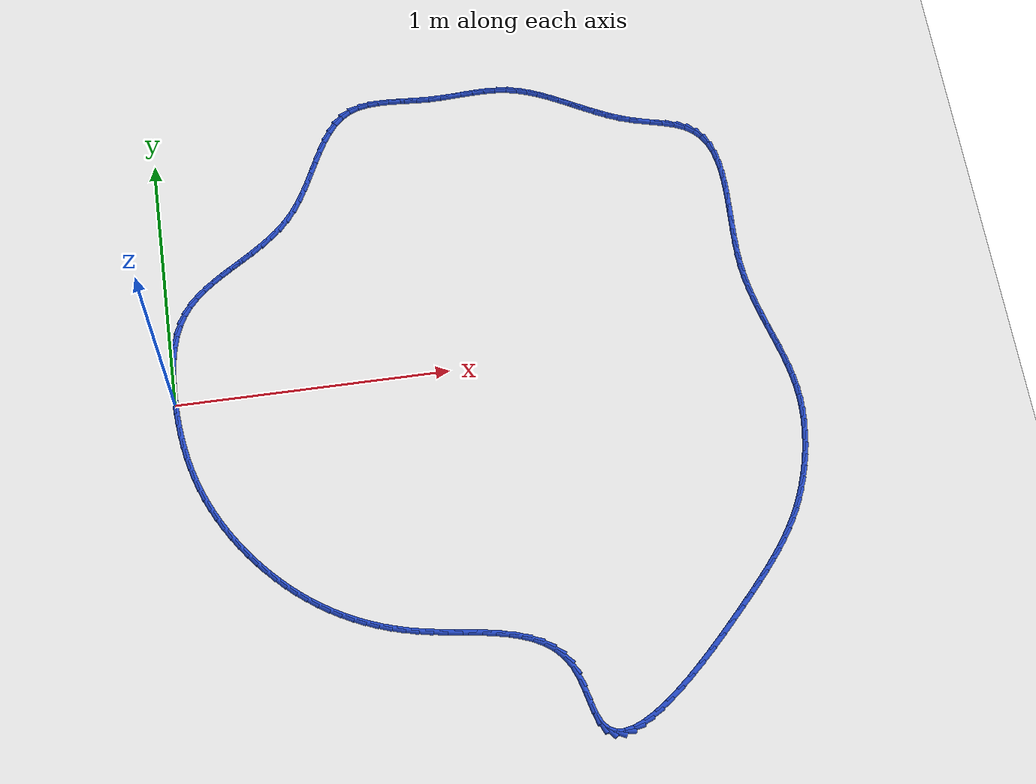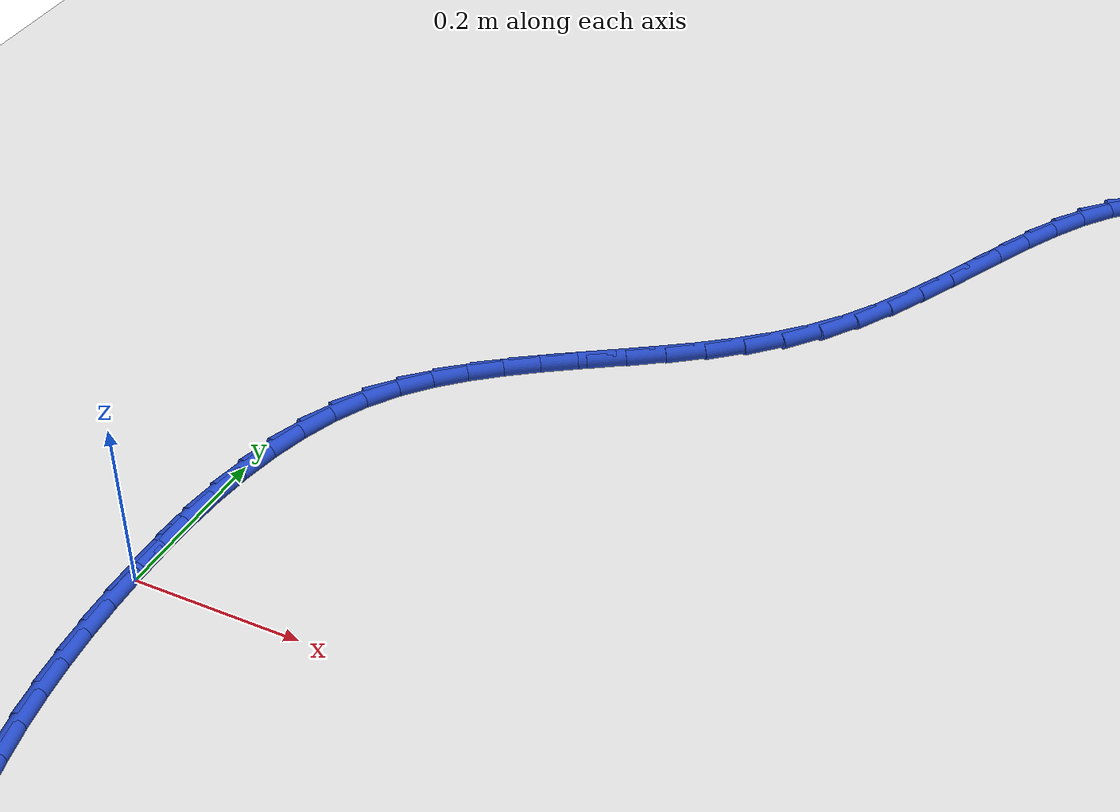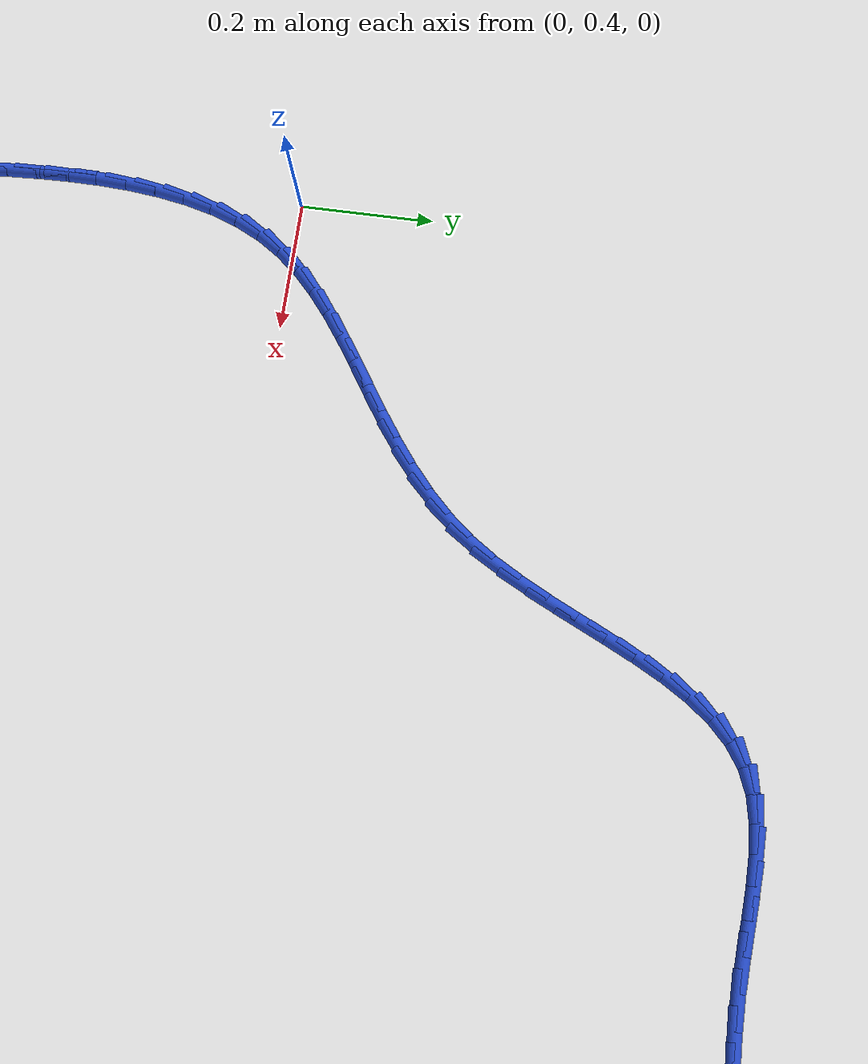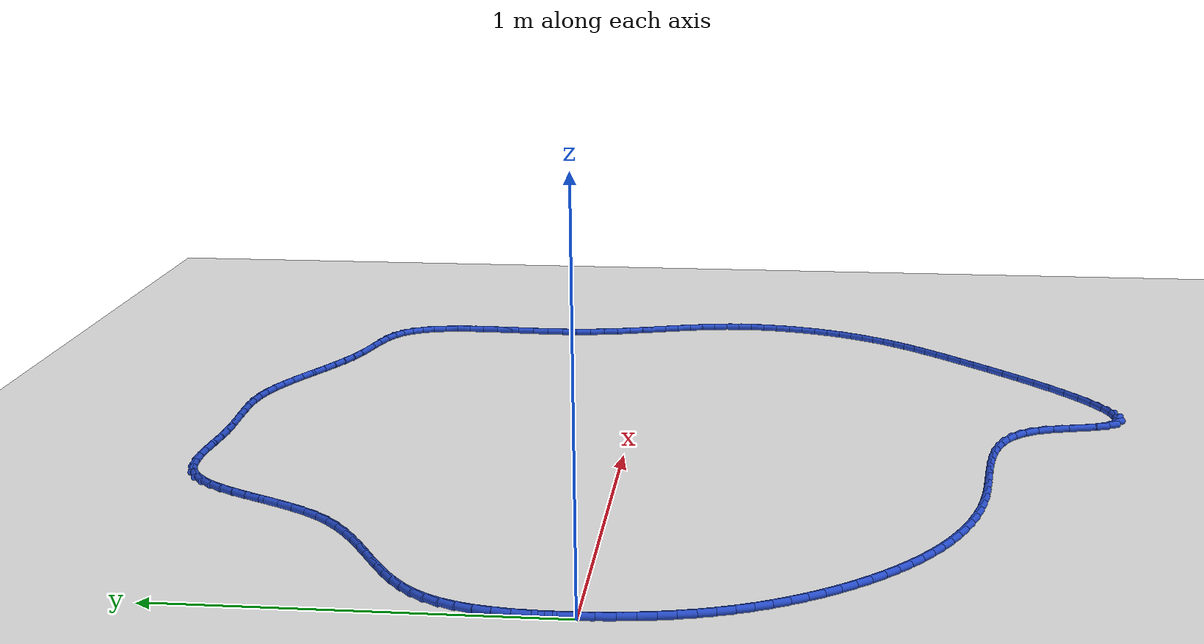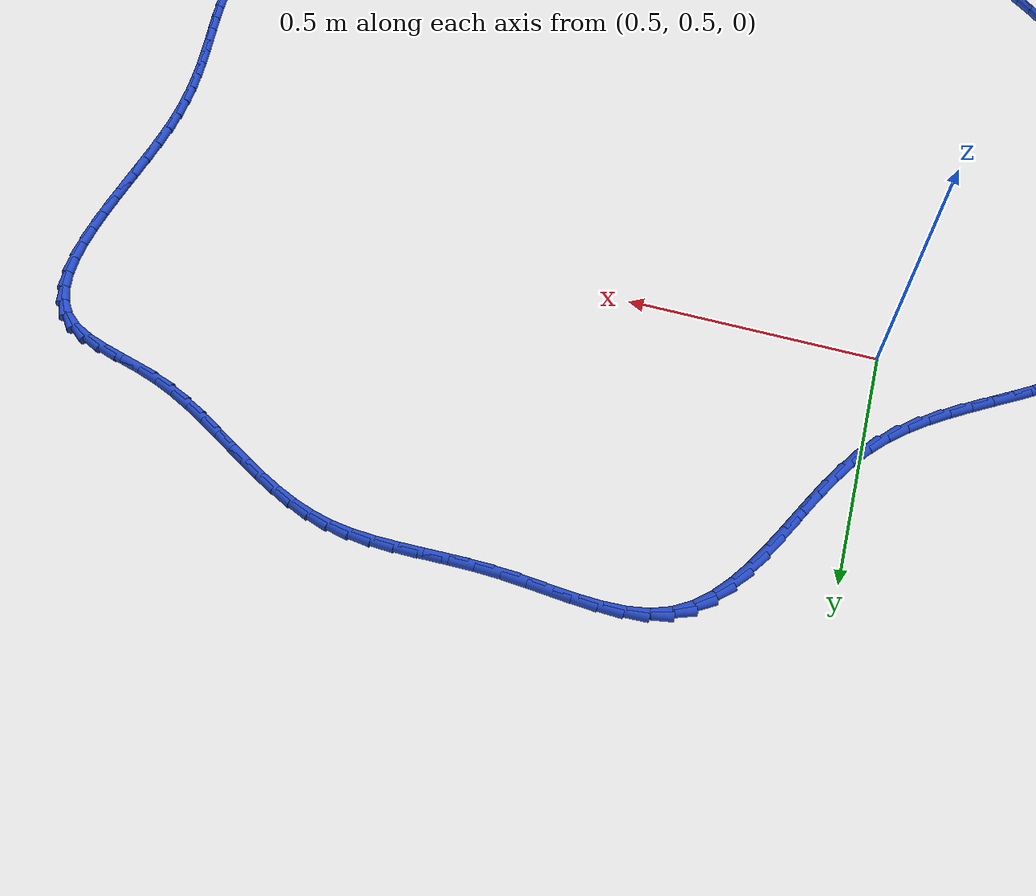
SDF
<sdf version="1.6">
 <world name="default">
  <light name="sun" type="directional">
   <pose>0 0 10 0 -0 0</pose>
   <diffuse>0.8 0.8 0.8 1</diffuse>
   <specular>0.2 0.2 0.2 1</specular>
   <attenuation>
    <range>1000</range>
    <constant>0.9</constant>
    <linear>0.01</linear>
    <quadratic>0.001</quadratic>
   </attenuation>
   <direction>-0.5 0.1 -0.9</direction>
  </light>
  <model name="ground_plane">
   <static>1</static>
   <link name="link">
    <collision name="collision">
     <geometry><plane><normal>0 0 1</normal><size>100 100</size></plane></geometry>
     <surface><friction><ode><mu>100</mu><mu2>50</mu2></ode></friction></surface>
    </collision>
    <visual name="visual">
     <cast_shadows>0</cast_shadows>
     <geometry><plane><normal>0 0 1</normal><size>100 100</size></plane></geometry>
     <material>
      <script><uri>file://media/materials/scripts/gazebo.material</uri><name>Gazebo/WhiteGlow</name></script>
     </material>
    </visual>
   </link>
  </model>
  <gravity>0 0 -9.8</gravity>
  <magnetic_field>6e-06 2.3e-05 -4.2e-05</magnetic_field>
  <atmosphere type="adiabatic"/>
  <physics name="default_physics" default="0" type="ode">
   <max_step_size>0.001</max_step_size>
   <real_time_factor>1</real_time_factor>
   <real_time_update_rate>1000</real_time_update_rate>
  </physics>
  <scene><ambient>0.4 0.4 0.4 1</ambient><background>0.7 0.7 0.7 1</background><shadows>1</shadows></scene>
  <spherical_coordinates>
   <surface_model>EARTH_WGS84</surface_model>
   <latitude_deg>0</latitude_deg>
   <longitude_deg>0</longitude_deg>
   <elevation>0</elevation>
   <heading_deg>0</heading_deg>
  </spherical_coordinates>
  <model name="line">
   <link name="link_0">
    <pose>-3.903127820947816e-17 -1.3877787807814457e-17 0.01 0 1.57 -1.5505914478385485</pose>
    <collision name="collision">
     <geometry><cylinder><radius>0.01</radius><length>0.08</length></cylinder></geometry>
    </collision>
    <visual name="visual">
     <material>
      <script><name>Gazebo/Blue</name><uri>file://media/materials/scripts/gazebo.material</uri></script>
     </material>
     <geometry><cylinder><radius>0.01</radius><length>0.08</length></cylinder></geometry>
    </visual>
   </link>
   <link name="link_1">
    <pose>-0.000938762816465074 0.04645586192666425 0.01 0 1.57 1.5552604086132704</pose>
    <collision name="collision">
     <geometry><cylinder><radius>0.01</radius><length>0.08</length></cylinder></geometry>
    </collision>
    <visual name="visual">
     <material>
      <script><name>Gazebo/Blue</name><uri>file://media/materials/scripts/gazebo.material</uri></script>
     </material>
     <geometry><cylinder><radius>0.01</radius><length>0.08</length></cylinder></geometry>
    </visual>
   </link>
   <link name="link_2">
    <pose>-0.00021346502682845583 0.09313732783327625 0.01 0 1.57 1.5110777956562365</pose>
    <collision name="collision">
     <geometry><cylinder><radius>0.01</radius><length>0.08</length></cylinder></geometry>
    </collision>
    <visual name="visual">
     <material>
      <script><name>Gazebo/Blue</name><uri>file://media/materials/scripts/gazebo.material</uri></script>
     </material>
     <geometry><cylinder><radius>0.01</radius><length>0.08</length></cylinder></geometry>
    </visual>
   </link>
   <link name="link_3">
    <pose>0.0025612118360466107 0.13954465868091998 0.01 0 1.57 1.4571314653900533</pose>
    <collision name="collision">
     <geometry><cylinder><radius>0.01</radius><length>0.08</length></cylinder></geometry>
    </collision>
    <visual name="visual">
     <material>
      <script><name>Gazebo/Blue</name><uri>file://media/materials/scripts/gazebo.material</uri></script>
     </material>
     <geometry><cylinder><radius>0.01</radius><length>0.08</length></cylinder></geometry>
    </visual>
   </link>
   <link name="link_4">
    <pose>0.007770586239296926 0.18517811543067966 0.01 0 1.57 1.3917292936854357</pose>
    <collision name="collision">
     <geometry><cylinder><radius>0.01</radius><length>0.08</length></cylinder></geometry>
    </collision>
    <visual name="visual">
     <material>
      <script><name>Gazebo/Blue</name><uri>file://media/materials/scripts/gazebo.material</uri></script>
     </material>
     <geometry><cylinder><radius>0.01</radius><length>0.08</length></cylinder></geometry>
    </visual>
   </link>
   <link name="link_5">
    <pose>0.015799976650059284 0.2295379590436391 0.01 0 1.57 1.312863221745212</pose>
    <collision name="collision">
     <geometry><cylinder><radius>0.01</radius><length>0.08</length></cylinder></geometry>
    </collision>
    <visual name="visual">
     <material>
      <script><name>Gazebo/Blue</name><uri>file://media/materials/scripts/gazebo.material</uri></script>
     </material>
     <geometry><cylinder><radius>0.01</radius><length>0.08</length></cylinder></geometry>
    </visual>
   </link>
   <link name="link_6">
    <pose>0.02703470153547047 0.27212445048088246 0.01 0 1.57 1.2183941921724666</pose>
    <collision name="collision">
     <geometry><cylinder><radius>0.01</radius><length>0.08</length></cylinder></geometry>
    </collision>
    <visual name="visual">
     <material>
      <script><name>Gazebo/Blue</name><uri>file://media/materials/scripts/gazebo.material</uri></script>
     </material>
     <geometry><cylinder><radius>0.01</radius><length>0.08</length></cylinder></geometry>
    </visual>
   </link>
   <link name="link_7">
    <pose>0.04186007936266729 0.3124378507034939 0.01 0 1.57 1.1064869490803277</pose>
    <collision name="collision">
     <geometry><cylinder><radius>0.01</radius><length>0.08</length></cylinder></geometry>
    </collision>
    <visual name="visual">
     <material>
      <script><name>Gazebo/Blue</name><uri>file://media/materials/scripts/gazebo.material</uri></script>
     </material>
     <geometry><cylinder><radius>0.01</radius><length>0.08</length></cylinder></geometry>
    </visual>
   </link>
   <link name="link_8">
    <pose>0.06066142859878655 0.34997842067255724 0.01 0 1.57 0.9782676961249377</pose>
    <collision name="collision">
     <geometry><cylinder><radius>0.01</radius><length>0.08</length></cylinder></geometry>
    </collision>
    <visual name="visual">
     <material>
      <script><name>Gazebo/Blue</name><uri>file://media/materials/scripts/gazebo.material</uri></script>
     </material>
     <geometry><cylinder><radius>0.01</radius><length>0.08</length></cylinder></geometry>
    </visual>
   </link>
   <link name="link_9">
    <pose>0.08376991908536607 0.38430352987943195 0.01 0 1.57 0.8561584060810647</pose>
    <collision name="collision">
     <geometry><cylinder><radius>0.01</radius><length>0.08</length></cylinder></geometry>
    </collision>
    <visual name="visual">
     <material>
      <script><name>Gazebo/Blue</name><uri>file://media/materials/scripts/gazebo.material</uri></script>
     </material>
     <geometry><cylinder><radius>0.01</radius><length>0.08</length></cylinder></geometry>
    </visual>
   </link>
   <link name="link_10">
    <pose>0.11092179225668829 0.41559799655644813 0.01 0 1.57 0.7563378923026677</pose>
    <collision name="collision">
     <geometry><cylinder><radius>0.01</radius><length>0.08</length></cylinder></geometry>
    </collision>
    <visual name="visual">
     <material>
      <script><name>Gazebo/Blue</name><uri>file://media/materials/scripts/gazebo.material</uri></script>
     </material>
     <geometry><cylinder><radius>0.01</radius><length>0.08</length></cylinder></geometry>
    </visual>
   </link>
   <link name="link_11">
    <pose>0.14148525771230414 0.4444347883477361 0.01 0 1.57 0.6799791299687572</pose>
    <collision name="collision">
     <geometry><cylinder><radius>0.01</radius><length>0.08</length></cylinder></geometry>
    </collision>
    <visual name="visual">
     <material>
      <script><name>Gazebo/Blue</name><uri>file://media/materials/scripts/gazebo.material</uri></script>
     </material>
     <geometry><cylinder><radius>0.01</radius><length>0.08</length></cylinder></geometry>
    </visual>
   </link>
   <link name="link_12">
    <pose>0.17482306322868 0.4713926332779629 0.01 0 1.57 0.6261677456062255</pose>
    <collision name="collision">
     <geometry><cylinder><radius>0.01</radius><length>0.08</length></cylinder></geometry>
    </collision>
    <visual name="visual">
     <material>
      <script><name>Gazebo/Blue</name><uri>file://media/materials/scripts/gazebo.material</uri></script>
     </material>
     <geometry><cylinder><radius>0.01</radius><length>0.08</length></cylinder></geometry>
    </visual>
   </link>
   <link name="link_13">
    <pose>0.21029795658228215 0.49705025937179553 0.01 0 1.57 0.5933443862915642</pose>
    <collision name="collision">
     <geometry><cylinder><radius>0.01</radius><length>0.08</length></cylinder></geometry>
    </collision>
    <visual name="visual">
     <material>
      <script><name>Gazebo/Blue</name><uri>file://media/materials/scripts/gazebo.material</uri></script>
     </material>
     <geometry><cylinder><radius>0.01</radius><length>0.08</length></cylinder></geometry>
    </visual>
   </link>
   <link name="link_14">
    <pose>0.24727268554957677 0.5219863946539012 0.01 0 1.57 0.5800658131835379</pose>
    <collision name="collision">
     <geometry><cylinder><radius>0.01</radius><length>0.08</length></cylinder></geometry>
    </collision>
    <visual name="visual">
     <material>
      <script><name>Gazebo/Blue</name><uri>file://media/materials/scripts/gazebo.material</uri></script>
     </material>
     <geometry><cylinder><radius>0.01</radius><length>0.08</length></cylinder></geometry>
    </visual>
   </link>
   <link name="link_15">
    <pose>0.2851099979070302 0.5467797671489468 0.01 0 1.57 0.5853467770314257</pose>
    <collision name="collision">
     <geometry><cylinder><radius>0.01</radius><length>0.08</length></cylinder></geometry>
    </collision>
    <visual name="visual">
     <material>
      <script><name>Gazebo/Blue</name><uri>file://media/materials/scripts/gazebo.material</uri></script>
     </material>
     <geometry><cylinder><radius>0.01</radius><length>0.08</length></cylinder></geometry>
    </visual>
   </link>
   <link name="link_16">
    <pose>0.32317264143110885 0.5720091048815996 0.01 0 1.57 0.6087361123308997</pose>
    <collision name="collision">
     <geometry><cylinder><radius>0.01</radius><length>0.08</length></cylinder></geometry>
    </collision>
    <visual name="visual">
     <material>
      <script><name>Gazebo/Blue</name><uri>file://media/materials/scripts/gazebo.material</uri></script>
     </material>
     <geometry><cylinder><radius>0.01</radius><length>0.08</length></cylinder></geometry>
    </visual>
   </link>
   <link name="link_17">
    <pose>0.3608233638982789 0.5982531358765265 0.01 0 1.57 0.6502214812099095</pose>
    <collision name="collision">
     <geometry><cylinder><radius>0.01</radius><length>0.08</length></cylinder></geometry>
    </collision>
    <visual name="visual">
     <material>
      <script><name>Gazebo/Blue</name><uri>file://media/materials/scripts/gazebo.material</uri></script>
     </material>
     <geometry><cylinder><radius>0.01</radius><length>0.08</length></cylinder></geometry>
    </visual>
   </link>
   <link name="link_18">
    <pose>0.3974249130850066 0.6260905881583947 0.01 0 1.57 0.7099843835716187</pose>
    <collision name="collision">
     <geometry><cylinder><radius>0.01</radius><length>0.08</length></cylinder></geometry>
    </collision>
    <visual name="visual">
     <material>
      <script><name>Gazebo/Blue</name><uri>file://media/materials/scripts/gazebo.material</uri></script>
     </material>
     <geometry><cylinder><radius>0.01</radius><length>0.08</length></cylinder></geometry>
    </visual>
   </link>
   <link name="link_19">
    <pose>0.4323400367677581 0.6561001897518708 0.01 0 1.57 0.7879846610081189</pose>
    <collision name="collision">
     <geometry><cylinder><radius>0.01</radius><length>0.08</length></cylinder></geometry>
    </collision>
    <visual name="visual">
     <material>
      <script><name>Gazebo/Blue</name><uri>file://media/materials/scripts/gazebo.material</uri></script>
     </material>
     <geometry><cylinder><radius>0.01</radius><length>0.08</length></cylinder></geometry>
    </visual>
   </link>
   <link name="link_20">
    <pose>0.4649314827230001 0.6888606686816225 0.01 0 1.57 0.8830834872635878</pose>
    <collision name="collision">
     <geometry><cylinder><radius>0.01</radius><length>0.08</length></cylinder></geometry>
    </collision>
    <visual name="visual">
     <material>
      <script><name>Gazebo/Blue</name><uri>file://media/materials/scripts/gazebo.material</uri></script>
     </material>
     <geometry><cylinder><radius>0.01</radius><length>0.08</length></cylinder></geometry>
    </visual>
   </link>
   <link name="link_21">
    <pose>0.4945708826316573 0.7249403574108669 0.01 0 1.57 0.9777289401478115</pose>
    <collision name="collision">
     <geometry><cylinder><radius>0.01</radius><length>0.08</length></cylinder></geometry>
    </collision>
    <visual name="visual">
     <material>
      <script><name>Gazebo/Blue</name><uri>file://media/materials/scripts/gazebo.material</uri></script>
     </material>
     <geometry><cylinder><radius>0.01</radius><length>0.08</length></cylinder></geometry>
    </visual>
   </link>
   <link name="link_22">
    <pose>0.5211214113356271 0.7643324058174049 0.01 0 1.57 1.0487846464671375</pose>
    <collision name="collision">
     <geometry><cylinder><radius>0.01</radius><length>0.08</length></cylinder></geometry>
    </collision>
    <visual name="visual">
     <material>
      <script><name>Gazebo/Blue</name><uri>file://media/materials/scripts/gazebo.material</uri></script>
     </material>
     <geometry><cylinder><radius>0.01</radius><length>0.08</length></cylinder></geometry>
    </visual>
   </link>
   <link name="link_23">
    <pose>0.5451851901173571 0.8061652805570834 0.01 0 1.57 1.0965948639715848</pose>
    <collision name="collision">
     <geometry><cylinder><radius>0.01</radius><length>0.08</length></cylinder></geometry>
    </collision>
    <visual name="visual">
     <material>
      <script><name>Gazebo/Blue</name><uri>file://media/materials/scripts/gazebo.material</uri></script>
     </material>
     <geometry><cylinder><radius>0.01</radius><length>0.08</length></cylinder></geometry>
    </visual>
   </link>
   <link name="link_24">
    <pose>0.5674252973785667 0.8494961188964985 0.01 0 1.57 1.1230122361032615</pose>
    <collision name="collision">
     <geometry><cylinder><radius>0.01</radius><length>0.08</length></cylinder></geometry>
    </collision>
    <visual name="visual">
     <material>
      <script><name>Gazebo/Blue</name><uri>file://media/materials/scripts/gazebo.material</uri></script>
     </material>
     <geometry><cylinder><radius>0.01</radius><length>0.08</length></cylinder></geometry>
    </visual>
   </link>
   <link name="link_25">
    <pose>0.5885048115209753 0.8933820581022464 0.01 0 1.57 1.128842787347342</pose>
    <collision name="collision">
     <geometry><cylinder><radius>0.01</radius><length>0.08</length></cylinder></geometry>
    </collision>
    <visual name="visual">
     <material>
      <script><name>Gazebo/Blue</name><uri>file://media/materials/scripts/gazebo.material</uri></script>
     </material>
     <geometry><cylinder><radius>0.01</radius><length>0.08</length></cylinder></geometry>
    </visual>
   </link>
   <link name="link_26">
    <pose>0.6090868109463021 0.9368802354409228 0.01 0 1.57 1.113547654454905</pose>
    <collision name="collision">
     <geometry><cylinder><radius>0.01</radius><length>0.08</length></cylinder></geometry>
    </collision>
    <visual name="visual">
     <material>
      <script><name>Gazebo/Blue</name><uri>file://media/materials/scripts/gazebo.material</uri></script>
     </material>
     <geometry><cylinder><radius>0.01</radius><length>0.08</length></cylinder></geometry>
    </visual>
   </link>
   <link name="link_27">
    <pose>0.6298343740562672 0.9790477881791244 0.01 0 1.57 1.0750148970025242</pose>
    <collision name="collision">
     <geometry><cylinder><radius>0.01</radius><length>0.08</length></cylinder></geometry>
    </collision>
    <visual name="visual">
     <material>
      <script><name>Gazebo/Blue</name><uri>file://media/materials/scripts/gazebo.material</uri></script>
     </material>
     <geometry><cylinder><radius>0.01</radius><length>0.08</length></cylinder></geometry>
    </visual>
   </link>
   <link name="link_28">
    <pose>0.6514105792525894 1.0189418535834471 0.01 0 1.57 1.0093718282133637</pose>
    <collision name="collision">
     <geometry><cylinder><radius>0.01</radius><length>0.08</length></cylinder></geometry>
    </collision>
    <visual name="visual">
     <material>
      <script><name>Gazebo/Blue</name><uri>file://media/materials/scripts/gazebo.material</uri></script>
     </material>
     <geometry><cylinder><radius>0.01</radius><length>0.08</length></cylinder></geometry>
    </visual>
   </link>
   <link name="link_29">
    <pose>0.6744785049369887 1.055619568920487 0.01 0 1.57 0.9110851317835824</pose>
    <collision name="collision">
     <geometry><cylinder><radius>0.01</radius><length>0.08</length></cylinder></geometry>
    </collision>
    <visual name="visual">
     <material>
      <script><name>Gazebo/Blue</name><uri>file://media/materials/scripts/gazebo.material</uri></script>
     </material>
     <geometry><cylinder><radius>0.01</radius><length>0.08</length></cylinder></geometry>
    </visual>
   </link>
   <link name="link_30">
    <pose>0.6997012295111842 1.0881380714568403 0.01 0 1.57 0.7741435303618186</pose>
    <collision name="collision">
     <geometry><cylinder><radius>0.01</radius><length>0.08</length></cylinder></geometry>
    </collision>
    <visual name="visual">
     <material>
      <script><name>Gazebo/Blue</name><uri>file://media/materials/scripts/gazebo.material</uri></script>
     </material>
     <geometry><cylinder><radius>0.01</radius><length>0.08</length></cylinder></geometry>
    </visual>
   </link>
   <link name="link_31">
    <pose>0.7277418313768955 1.1155544984591035 0.01 0 1.57 0.5958050045412697</pose>
    <collision name="collision">
     <geometry><cylinder><radius>0.01</radius><length>0.08</length></cylinder></geometry>
    </collision>
    <visual name="visual">
     <material>
      <script><name>Gazebo/Blue</name><uri>file://media/materials/scripts/gazebo.material</uri></script>
     </material>
     <geometry><cylinder><radius>0.01</radius><length>0.08</length></cylinder></geometry>
    </visual>
   </link>
   <link name="link_32">
    <pose>0.7592633889358422 1.1369259871938717 0.01 0 1.57 0.3859506271365281</pose>
    <collision name="collision">
     <geometry><cylinder><radius>0.01</radius><length>0.08</length></cylinder></geometry>
    </collision>
    <visual name="visual">
     <material>
      <script><name>Gazebo/Blue</name><uri>file://media/materials/scripts/gazebo.material</uri></script>
     </material>
     <geometry><cylinder><radius>0.01</radius><length>0.08</length></cylinder></geometry>
    </visual>
   </link>
   <link name="link_33">
    <pose>0.7948770134945562 1.1513968419011515 0.01 0 1.57 0.2000328599117744</pose>
    <collision name="collision">
     <geometry><cylinder><radius>0.01</radius><length>0.08</length></cylinder></geometry>
    </collision>
    <visual name="visual">
     <material>
      <script><name>Gazebo/Blue</name><uri>file://media/materials/scripts/gazebo.material</uri></script>
     </material>
     <geometry><cylinder><radius>0.01</radius><length>0.08</length></cylinder></geometry>
    </visual>
   </link>
   <link name="link_34">
    <pose>0.8344175385846238 1.1594134558432942 0.01 0 1.57 0.07036660356365947</pose>
    <collision name="collision">
     <geometry><cylinder><radius>0.01</radius><length>0.08</length></cylinder></geometry>
    </collision>
    <visual name="visual">
     <material>
      <script><name>Gazebo/Blue</name><uri>file://media/materials/scripts/gazebo.material</uri></script>
     </material>
     <geometry><cylinder><radius>0.01</radius><length>0.08</length></cylinder></geometry>
    </visual>
   </link>
   <link name="link_35">
    <pose>0.8771228837683843 1.1624234555418365 0.01 0 1.57 -0.011604383951390866</pose>
    <collision name="collision">
     <geometry><cylinder><radius>0.01</radius><length>0.08</length></cylinder></geometry>
    </collision>
    <visual name="visual">
     <material>
      <script><name>Gazebo/Blue</name><uri>file://media/materials/scripts/gazebo.material</uri></script>
     </material>
     <geometry><cylinder><radius>0.01</radius><length>0.08</length></cylinder></geometry>
    </visual>
   </link>
   <link name="link_36">
    <pose>0.9222156523390947 1.1619001582523276 0.01 0 1.57 -0.05525680608570604</pose>
    <collision name="collision">
     <geometry><cylinder><radius>0.01</radius><length>0.08</length></cylinder></geometry>
    </collision>
    <visual name="visual">
     <material>
      <script><name>Gazebo/Blue</name><uri>file://media/materials/scripts/gazebo.material</uri></script>
     </material>
     <geometry><cylinder><radius>0.01</radius><length>0.08</length></cylinder></geometry>
    </visual>
   </link>
   <link name="link_37">
    <pose>0.9689184475900112 1.1593168812303176 0.01 0 1.57 -0.0665872467622741</pose>
    <collision name="collision">
     <geometry><cylinder><radius>0.01</radius><length>0.08</length></cylinder></geometry>
    </collision>
    <visual name="visual">
     <material>
      <script><name>Gazebo/Blue</name><uri>file://media/materials/scripts/gazebo.material</uri></script>
     </material>
     <geometry><cylinder><radius>0.01</radius><length>0.08</length></cylinder></geometry>
    </visual>
   </link>
   <link name="link_38">
    <pose>1.0164538728143908 1.156146941731356 0.01 0 1.57 -0.04794082038904211</pose>
    <collision name="collision">
     <geometry><cylinder><radius>0.01</radius><length>0.08</length></cylinder></geometry>
    </collision>
    <visual name="visual">
     <material>
      <script><name>Gazebo/Blue</name><uri>file://media/materials/scripts/gazebo.material</uri></script>
     </material>
     <geometry><cylinder><radius>0.01</radius><length>0.08</length></cylinder></geometry>
    </visual>
   </link>
   <link name="link_39">
    <pose>1.06404453130549 1.153863657010992 0.01 0 1.57 -0.004198208526718472</pose>
    <collision name="collision">
     <geometry><cylinder><radius>0.01</radius><length>0.08</length></cylinder></geometry>
    </collision>
    <visual name="visual">
     <material>
      <script><name>Gazebo/Blue</name><uri>file://media/materials/scripts/gazebo.material</uri></script>
     </material>
     <geometry><cylinder><radius>0.01</radius><length>0.08</length></cylinder></geometry>
    </visual>
   </link>
   <link name="link_40">
    <pose>1.110997548314537 1.1536665372965527 0.01 0 1.57 0.03234485522576058</pose>
    <collision name="collision">
     <geometry><cylinder><radius>0.01</radius><length>0.08</length></cylinder></geometry>
    </collision>
    <visual name="visual">
     <material>
      <script><name>Gazebo/Blue</name><uri>file://media/materials/scripts/gazebo.material</uri></script>
     </material>
     <geometry><cylinder><radius>0.01</radius><length>0.08</length></cylinder></geometry>
    </visual>
   </link>
   <link name="link_41">
    <pose>1.1571128575357317 1.155158650677829 0.01 0 1.57 0.04873802280955987</pose>
    <collision name="collision">
     <geometry><cylinder><radius>0.01</radius><length>0.08</length></cylinder></geometry>
    </collision>
    <visual name="visual">
     <material>
      <script><name>Gazebo/Blue</name><uri>file://media/materials/scripts/gazebo.material</uri></script>
     </material>
     <geometry><cylinder><radius>0.01</radius><length>0.08</length></cylinder></geometry>
    </visual>
   </link>
   <link name="link_42">
    <pose>1.2023685064215683 1.157366069632889 0.01 0 1.57 0.043871357113652434</pose>
    <collision name="collision">
     <geometry><cylinder><radius>0.01</radius><length>0.08</length></cylinder></geometry>
    </collision>
    <visual name="visual">
     <material>
      <script><name>Gazebo/Blue</name><uri>file://media/materials/scripts/gazebo.material</uri></script>
     </material>
     <geometry><cylinder><radius>0.01</radius><length>0.08</length></cylinder></geometry>
    </visual>
   </link>
   <link name="link_43">
    <pose>1.246742785435816 1.1593140794101016 0.01 0 1.57 0.016420565573988834</pose>
    <collision name="collision">
     <geometry><cylinder><radius>0.01</radius><length>0.08</length></cylinder></geometry>
    </collision>
    <visual name="visual">
     <material>
      <script><name>Gazebo/Blue</name><uri>file://media/materials/scripts/gazebo.material</uri></script>
     </material>
     <geometry><cylinder><radius>0.01</radius><length>0.08</length></cylinder></geometry>
    </visual>
   </link>
   <link name="link_44">
    <pose>1.290213985042246 1.1600279652578362 0.01 0 1.57 -0.0351225412080842</pose>
    <collision name="collision">
     <geometry><cylinder><radius>0.01</radius><length>0.08</length></cylinder></geometry>
    </collision>
    <visual name="visual">
     <material>
      <script><name>Gazebo/Blue</name><uri>file://media/materials/scripts/gazebo.material</uri></script>
     </material>
     <geometry><cylinder><radius>0.01</radius><length>0.08</length></cylinder></geometry>
    </visual>
   </link>
   <link name="link_45">
    <pose>1.3327603957046292 1.1585330124244628 0.01 0 1.57 -0.11199373843666105</pose>
    <collision name="collision">
     <geometry><cylinder><radius>0.01</radius><length>0.08</length></cylinder></geometry>
    </collision>
    <visual name="visual">
     <material>
      <script><name>Gazebo/Blue</name><uri>file://media/materials/scripts/gazebo.material</uri></script>
     </material>
     <geometry><cylinder><radius>0.01</radius><length>0.08</length></cylinder></geometry>
    </visual>
   </link>
   <link name="link_46">
    <pose>1.3743603078867341 1.1538545061583505 0.01 0 1.57 -0.21078741598733972</pose>
    <collision name="collision">
     <geometry><cylinder><radius>0.01</radius><length>0.08</length></cylinder></geometry>
    </collision>
    <visual name="visual">
     <material>
      <script><name>Gazebo/Blue</name><uri>file://media/materials/scripts/gazebo.material</uri></script>
     </material>
     <geometry><cylinder><radius>0.01</radius><length>0.08</length></cylinder></geometry>
    </visual>
   </link>
   <link name="link_47">
    <pose>1.4150138104141474 1.1451560481546044 0.01 0 1.57 -0.3042017643822353</pose>
    <collision name="collision">
     <geometry><cylinder><radius>0.01</radius><length>0.08</length></cylinder></geometry>
    </collision>
    <visual name="visual">
     <material>
      <script><name>Gazebo/Blue</name><uri>file://media/materials/scripts/gazebo.material</uri></script>
     </material>
     <geometry><cylinder><radius>0.01</radius><length>0.08</length></cylinder></geometry>
    </visual>
   </link>
   <link name="link_48">
    <pose>1.4548845089174283 1.1326387980513701 0.01 0 1.57 -0.3790475046889929</pose>
    <collision name="collision">
     <geometry><cylinder><radius>0.01</radius><length>0.08</length></cylinder></geometry>
    </collision>
    <visual name="visual">
     <material>
      <script><name>Gazebo/Blue</name><uri>file://media/materials/scripts/gazebo.material</uri></script>
     </material>
     <geometry><cylinder><radius>0.01</radius><length>0.08</length></cylinder></geometry>
    </visual>
   </link>
   <link name="link_49">
    <pose>1.494210252837821 1.1169750123597295 0.01 0 1.57 -0.4350863418128398</pose>
    <collision name="collision">
     <geometry><cylinder><radius>0.01</radius><length>0.08</length></cylinder></geometry>
    </collision>
    <visual name="visual">
     <material>
      <script><name>Gazebo/Blue</name><uri>file://media/materials/scripts/gazebo.material</uri></script>
     </material>
     <geometry><cylinder><radius>0.01</radius><length>0.08</length></cylinder></geometry>
    </visual>
   </link>
   <link name="link_50">
    <pose>1.5332292627851345 1.098839302754758 0.01 0 1.57 -0.4730055033617569</pose>
    <collision name="collision">
     <geometry><cylinder><radius>0.01</radius><length>0.08</length></cylinder></geometry>
    </collision>
    <visual name="visual">
     <material>
      <script><name>Gazebo/Blue</name><uri>file://media/materials/scripts/gazebo.material</uri></script>
     </material>
     <geometry><cylinder><radius>0.01</radius><length>0.08</length></cylinder></geometry>
    </visual>
   </link>
   <link name="link_51">
    <pose>1.572179759369175 1.0789062809115295 0.01 0 1.57 -0.49376294823729433</pose>
    <collision name="collision">
     <geometry><cylinder><radius>0.01</radius><length>0.08</length></cylinder></geometry>
    </collision>
    <visual name="visual">
     <material>
      <script><name>Gazebo/Blue</name><uri>file://media/materials/scripts/gazebo.material</uri></script>
     </material>
     <geometry><cylinder><radius>0.01</radius><length>0.08</length></cylinder></geometry>
    </visual>
   </link>
   <link name="link_52">
    <pose>1.6112999631997522 1.0578505585051194 0.01 0 1.57 -0.49823492725935536</pose>
    <collision name="collision">
     <geometry><cylinder><radius>0.01</radius><length>0.08</length></cylinder></geometry>
    </collision>
    <visual name="visual">
     <material>
      <script><name>Gazebo/Blue</name><uri>file://media/materials/scripts/gazebo.material</uri></script>
     </material>
     <geometry><cylinder><radius>0.01</radius><length>0.08</length></cylinder></geometry>
    </visual>
   </link>
   <link name="link_53">
    <pose>1.650828094886672 1.036346747210602 0.01 0 1.57 -0.4870654870112347</pose>
    <collision name="collision">
     <geometry><cylinder><radius>0.01</radius><length>0.08</length></cylinder></geometry>
    </collision>
    <visual name="visual">
     <material>
      <script><name>Gazebo/Blue</name><uri>file://media/materials/scripts/gazebo.material</uri></script>
     </material>
     <geometry><cylinder><radius>0.01</radius><length>0.08</length></cylinder></geometry>
    </visual>
   </link>
   <link name="link_54">
    <pose>1.6910023750397438 1.015069458703052 0.01 0 1.57 -0.4606587329476451</pose>
    <collision name="collision">
     <geometry><cylinder><radius>0.01</radius><length>0.08</length></cylinder></geometry>
    </collision>
    <visual name="visual">
     <material>
      <script><name>Gazebo/Blue</name><uri>file://media/materials/scripts/gazebo.material</uri></script>
     </material>
     <geometry><cylinder><radius>0.01</radius><length>0.08</length></cylinder></geometry>
    </visual>
   </link>
   <link name="link_55">
    <pose>1.7320610242687746 0.994693304657544 0.01 0 1.57 -0.4192768380145108</pose>
    <collision name="collision">
     <geometry><cylinder><radius>0.01</radius><length>0.08</length></cylinder></geometry>
    </collision>
    <visual name="visual">
     <material>
      <script><name>Gazebo/Blue</name><uri>file://media/materials/scripts/gazebo.material</uri></script>
     </material>
     <geometry><cylinder><radius>0.01</radius><length>0.08</length></cylinder></geometry>
    </visual>
   </link>
   <link name="link_56">
    <pose>1.7742422631835724 0.9758928967491531 0.01 0 1.57 -0.36322871391904715</pose>
    <collision name="collision">
     <geometry><cylinder><radius>0.01</radius><length>0.08</length></cylinder></geometry>
    </collision>
    <visual name="visual">
     <material>
      <script><name>Gazebo/Blue</name><uri>file://media/materials/scripts/gazebo.material</uri></script>
     </material>
     <geometry><cylinder><radius>0.01</radius><length>0.08</length></cylinder></geometry>
    </visual>
   </link>
   <link name="link_57">
    <pose>1.8177843123939452 0.9593428466529542 0.01 0 1.57 -0.2954070629744661</pose>
    <collision name="collision">
     <geometry><cylinder><radius>0.01</radius><length>0.08</length></cylinder></geometry>
    </collision>
    <visual name="visual">
     <material>
      <script><name>Gazebo/Blue</name><uri>file://media/materials/scripts/gazebo.material</uri></script>
     </material>
     <geometry><cylinder><radius>0.01</radius><length>0.08</length></cylinder></geometry>
    </visual>
   </link>
   <link name="link_58">
    <pose>1.8628540300178067 0.9456276392439706 0.01 0 1.57 -0.2498878609789018</pose>
    <collision name="collision">
     <geometry><cylinder><radius>0.01</radius><length>0.08</length></cylinder></geometry>
    </collision>
    <visual name="visual">
     <material>
      <script><name>Gazebo/Blue</name><uri>file://media/materials/scripts/gazebo.material</uri></script>
     </material>
     <geometry><cylinder><radius>0.01</radius><length>0.08</length></cylinder></geometry>
    </visual>
   </link>
   <link name="link_59">
    <pose>1.9085384145220865 0.9339679575979397 0.01 0 1.57 -0.2513917049845334</pose>
    <collision name="collision">
     <geometry><cylinder><radius>0.01</radius><length>0.08</length></cylinder></geometry>
    </collision>
    <visual name="visual">
     <material>
      <script><name>Gazebo/Blue</name><uri>file://media/materials/scripts/gazebo.material</uri></script>
     </material>
     <geometry><cylinder><radius>0.01</radius><length>0.08</length></cylinder></geometry>
    </visual>
   </link>
   <link name="link_60">
    <pose>1.9530869719489894 0.9225267791205228 0.01 0 1.57 -0.30451966435565186</pose>
    <collision name="collision">
     <geometry><cylinder><radius>0.01</radius><length>0.08</length></cylinder></geometry>
    </collision>
    <visual name="visual">
     <material>
      <script><name>Gazebo/Blue</name><uri>file://media/materials/scripts/gazebo.material</uri></script>
     </material>
     <geometry><cylinder><radius>0.01</radius><length>0.08</length></cylinder></geometry>
    </visual>
   </link>
   <link name="link_61">
    <pose>1.9947273030990926 0.9094394161333896 0.01 0 1.57 -0.42209693320861746</pose>
    <collision name="collision">
     <geometry><cylinder><radius>0.01</radius><length>0.08</length></cylinder></geometry>
    </collision>
    <visual name="visual">
     <material>
      <script><name>Gazebo/Blue</name><uri>file://media/materials/scripts/gazebo.material</uri></script>
     </material>
     <geometry><cylinder><radius>0.01</radius><length>0.08</length></cylinder></geometry>
    </visual>
   </link>
   <link name="link_62">
    <pose>2.0316870087729737 0.8928411809582103 0.01 0 1.57 -0.6189009591467636</pose>
    <collision name="collision">
     <geometry><cylinder><radius>0.01</radius><length>0.08</length></cylinder></geometry>
    </collision>
    <visual name="visual">
     <material>
      <script><name>Gazebo/Blue</name><uri>file://media/materials/scripts/gazebo.material</uri></script>
     </material>
     <geometry><cylinder><radius>0.01</radius><length>0.08</length></cylinder></geometry>
    </visual>
   </link>
   <link name="link_63">
    <pose>2.0623388024996623 0.8710094064817644 0.01 0 1.57 -0.8467380979680816</pose>
    <collision name="collision">
     <geometry><cylinder><radius>0.01</radius><length>0.08</length></cylinder></geometry>
    </collision>
    <visual name="visual">
     <material>
      <script><name>Gazebo/Blue</name><uri>file://media/materials/scripts/gazebo.material</uri></script>
     </material>
     <geometry><cylinder><radius>0.01</radius><length>0.08</length></cylinder></geometry>
    </visual>
   </link>
   <link name="link_64">
    <pose>2.086524150275121 0.843658880854676 0.01 0 1.57 -1.0529227244560257</pose>
    <collision name="collision">
     <geometry><cylinder><radius>0.01</radius><length>0.08</length></cylinder></geometry>
    </collision>
    <visual name="visual">
     <material>
      <script><name>Gazebo/Blue</name><uri>file://media/materials/scripts/gazebo.material</uri></script>
     </material>
     <geometry><cylinder><radius>0.01</radius><length>0.08</length></cylinder></geometry>
    </visual>
   </link>
   <link name="link_65">
    <pose>2.104937836101641 0.811339527138002 0.01 0 1.57 -1.2222245061837407</pose>
    <collision name="collision">
     <geometry><cylinder><radius>0.01</radius><length>0.08</length></cylinder></geometry>
    </collision>
    <visual name="visual">
     <material>
      <script><name>Gazebo/Blue</name><uri>file://media/materials/scripts/gazebo.material</uri></script>
     </material>
     <geometry><cylinder><radius>0.01</radius><length>0.08</length></cylinder></geometry>
    </visual>
   </link>
   <link name="link_66">
    <pose>2.1182851733218304 0.7746115733665817 0.01 0 1.57 -1.3528475350625297</pose>
    <collision name="collision">
     <geometry><cylinder><radius>0.01</radius><length>0.08</length></cylinder></geometry>
    </collision>
    <visual name="visual">
     <material>
      <script><name>Gazebo/Blue</name><uri>file://media/materials/scripts/gazebo.material</uri></script>
     </material>
     <geometry><cylinder><radius>0.01</radius><length>0.08</length></cylinder></geometry>
    </visual>
   </link>
   <link name="link_67">
    <pose>2.127271475278296 0.7340352475752551 0.01 0 1.57 -1.4498654368503014</pose>
    <collision name="collision">
     <geometry><cylinder><radius>0.01</radius><length>0.08</length></cylinder></geometry>
    </collision>
    <visual name="visual">
     <material>
      <script><name>Gazebo/Blue</name><uri>file://media/materials/scripts/gazebo.material</uri></script>
     </material>
     <geometry><cylinder><radius>0.01</radius><length>0.08</length></cylinder></geometry>
    </visual>
   </link>
   <link name="link_68">
    <pose>2.1326020553136464 0.6901707777988607 0.01 0 1.57 -1.5197557079551678</pose>
    <collision name="collision">
     <geometry><cylinder><radius>0.01</radius><length>0.08</length></cylinder></geometry>
    </collision>
    <visual name="visual">
     <material>
      <script><name>Gazebo/Blue</name><uri>file://media/materials/scripts/gazebo.material</uri></script>
     </material>
     <geometry><cylinder><radius>0.01</radius><length>0.08</length></cylinder></geometry>
    </visual>
   </link>
   <link name="link_69">
    <pose>2.134982226770488 0.6435783920722391 0.01 0 1.57 -1.5680261120408368</pose>
    <collision name="collision">
     <geometry><cylinder><radius>0.01</radius><length>0.08</length></cylinder></geometry>
    </collision>
    <visual name="visual">
     <material>
      <script><name>Gazebo/Blue</name><uri>file://media/materials/scripts/gazebo.material</uri></script>
     </material>
     <geometry><cylinder><radius>0.01</radius><length>0.08</length></cylinder></geometry>
    </visual>
   </link>
   <link name="link_70">
    <pose>2.1351173029914294 0.5948183184302296 0.01 0 1.57 1.5429144443698208</pose>
    <collision name="collision">
     <geometry><cylinder><radius>0.01</radius><length>0.08</length></cylinder></geometry>
    </collision>
    <visual name="visual">
     <material>
      <script><name>Gazebo/Blue</name><uri>file://media/materials/scripts/gazebo.material</uri></script>
     </material>
     <geometry><cylinder><radius>0.01</radius><length>0.08</length></cylinder></geometry>
    </visual>
   </link>
   <link name="link_71">
    <pose>2.1337125973190787 0.5444507849076707 0.01 0 1.57 1.5272726399565413</pose>
    <collision name="collision">
     <geometry><cylinder><radius>0.01</radius><length>0.08</length></cylinder></geometry>
    </collision>
    <visual name="visual">
     <material>
      <script><name>Gazebo/Blue</name><uri>file://media/materials/scripts/gazebo.material</uri></script>
     </material>
     <geometry><cylinder><radius>0.01</radius><length>0.08</length></cylinder></geometry>
    </visual>
   </link>
   <link name="link_72">
    <pose>2.1314734230960433 0.49303601953940324 0.01 0 1.57 1.525196961875671</pose>
    <collision name="collision">
     <geometry><cylinder><radius>0.01</radius><length>0.08</length></cylinder></geometry>
    </collision>
    <visual name="visual">
     <material>
      <script><name>Gazebo/Blue</name><uri>file://media/materials/scripts/gazebo.material</uri></script>
     </material>
     <geometry><cylinder><radius>0.01</radius><length>0.08</length></cylinder></geometry>
    </visual>
   </link>
   <link name="link_73">
    <pose>2.12910509366493 0.4411342503602661 0.01 0 1.57 1.5362312524247037</pose>
    <collision name="collision">
     <geometry><cylinder><radius>0.01</radius><length>0.08</length></cylinder></geometry>
    </collision>
    <visual name="visual">
     <material>
      <script><name>Gazebo/Blue</name><uri>file://media/materials/scripts/gazebo.material</uri></script>
     </material>
     <geometry><cylinder><radius>0.01</radius><length>0.08</length></cylinder></geometry>
    </visual>
   </link>
   <link name="link_74">
    <pose>2.127312922368348 0.3893057054050982 0.01 0 1.57 1.560821095706672</pose>
    <collision name="collision">
     <geometry><cylinder><radius>0.01</radius><length>0.08</length></cylinder></geometry>
    </collision>
    <visual name="visual">
     <material>
      <script><name>Gazebo/Blue</name><uri>file://media/materials/scripts/gazebo.material</uri></script>
     </material>
     <geometry><cylinder><radius>0.01</radius><length>0.08</length></cylinder></geometry>
    </visual>
   </link>
   <link name="link_75">
    <pose>2.1268022225489043 0.33811061270874027 0.01 0 1.57 -1.5412840318444692</pose>
    <collision name="collision">
     <geometry><cylinder><radius>0.01</radius><length>0.08</length></cylinder></geometry>
    </collision>
    <visual name="visual">
     <material>
      <script><name>Gazebo/Blue</name><uri>file://media/materials/scripts/gazebo.material</uri></script>
     </material>
     <geometry><cylinder><radius>0.01</radius><length>0.08</length></cylinder></geometry>
    </visual>
   </link>
   <link name="link_76">
    <pose>2.1282783075492064 0.28810920030603104 0.01 0 1.57 -1.4878564782083938</pose>
    <collision name="collision">
     <geometry><cylinder><radius>0.01</radius><length>0.08</length></cylinder></geometry>
    </collision>
    <visual name="visual">
     <material>
      <script><name>Gazebo/Blue</name><uri>file://media/materials/scripts/gazebo.material</uri></script>
     </material>
     <geometry><cylinder><radius>0.01</radius><length>0.08</length></cylinder></geometry>
    </visual>
   </link>
   <link name="link_77">
    <pose>2.1322975016223276 0.23976122432787927 0.01 0 1.57 -1.4355399842145602</pose>
    <collision name="collision">
     <geometry><cylinder><radius>0.01</radius><length>0.08</length></cylinder></geometry>
    </collision>
    <visual name="visual">
     <material>
      <script><name>Gazebo/Blue</name><uri>file://media/materials/scripts/gazebo.material</uri></script>
     </material>
     <geometry><cylinder><radius>0.01</radius><length>0.08</length></cylinder></geometry>
    </visual>
   </link>
   <link name="link_78">
    <pose>2.1386589523724764 0.19301583318378168 0.01 0 1.57 -1.3905914639191375</pose>
    <collision name="collision">
     <geometry><cylinder><radius>0.01</radius><length>0.08</length></cylinder></geometry>
    </collision>
    <visual name="visual">
     <material>
      <script><name>Gazebo/Blue</name><uri>file://media/materials/scripts/gazebo.material</uri></script>
     </material>
     <geometry><cylinder><radius>0.01</radius><length>0.08</length></cylinder></geometry>
    </visual>
   </link>
   <link name="link_79">
    <pose>2.146921864673398 0.1476603681130616 0.01 0 1.57 -1.3541539418036366</pose>
    <collision name="collision">
     <geometry><cylinder><radius>0.01</radius><length>0.08</length></cylinder></geometry>
    </collision>
    <visual name="visual">
     <material>
      <script><name>Gazebo/Blue</name><uri>file://media/materials/scripts/gazebo.material</uri></script>
     </material>
     <geometry><cylinder><radius>0.01</radius><length>0.08</length></cylinder></geometry>
    </visual>
   </link>
   <link name="link_80">
    <pose>2.156645347340759 0.10348210557756427 0.01 0 1.57 -1.3271310527742706</pose>
    <collision name="collision">
     <geometry><cylinder><radius>0.01</radius><length>0.08</length></cylinder></geometry>
    </collision>
    <visual name="visual">
     <material>
      <script><name>Gazebo/Blue</name><uri>file://media/materials/scripts/gazebo.material</uri></script>
     </material>
     <geometry><cylinder><radius>0.01</radius><length>0.08</length></cylinder></geometry>
    </visual>
   </link>
   <link name="link_81">
    <pose>2.16738850919023 0.06026832203913367 0.01 0 1.57 -1.310221586917291</pose>
    <collision name="collision">
     <geometry><cylinder><radius>0.01</radius><length>0.08</length></cylinder></geometry>
    </collision>
    <visual name="visual">
     <material>
      <script><name>Gazebo/Blue</name><uri>file://media/materials/scripts/gazebo.material</uri></script>
     </material>
     <geometry><cylinder><radius>0.01</radius><length>0.08</length></cylinder></geometry>
    </visual>
   </link>
   <link name="link_82">
    <pose>2.178710459037477 0.01780629395961373 0.01 0 1.57 -1.303960411278415</pose>
    <collision name="collision">
     <geometry><cylinder><radius>0.01</radius><length>0.08</length></cylinder></geometry>
    </collision>
    <visual name="visual">
     <material>
      <script><name>Gazebo/Blue</name><uri>file://media/materials/scripts/gazebo.material</uri></script>
     </material>
     <geometry><cylinder><radius>0.01</radius><length>0.08</length></cylinder></geometry>
    </visual>
   </link>
   <link name="link_83">
    <pose>2.190170305698171 -0.02411670219915032 0.01 0 1.57 -1.3087490281460987</pose>
    <collision name="collision">
     <geometry><cylinder><radius>0.01</radius><length>0.08</length></cylinder></geometry>
    </collision>
    <visual name="visual">
     <material>
      <script><name>Gazebo/Blue</name><uri>file://media/materials/scripts/gazebo.material</uri></script>
     </material>
     <geometry><cylinder><radius>0.01</radius><length>0.08</length></cylinder></geometry>
    </visual>
   </link>
   <link name="link_84">
    <pose>2.2013271579879783 -0.0657133899753149 0.01 0 1.57 -1.3248606555706637</pose>
    <collision name="collision">
     <geometry><cylinder><radius>0.01</radius><length>0.08</length></cylinder></geometry>
    </collision>
    <visual name="visual">
     <material>
      <script><name>Gazebo/Blue</name><uri>file://media/materials/scripts/gazebo.material</uri></script>
     </material>
     <geometry><cylinder><radius>0.01</radius><length>0.08</length></cylinder></geometry>
    </visual>
   </link>
   <link name="link_85">
    <pose>2.211740124722569 -0.1071964929070348 0.01 0 1.57 -1.3524094646093547</pose>
    <collision name="collision">
     <geometry><cylinder><radius>0.01</radius><length>0.08</length></cylinder></geometry>
    </collision>
    <visual name="visual">
     <material>
      <script><name>Gazebo/Blue</name><uri>file://media/materials/scripts/gazebo.material</uri></script>
     </material>
     <geometry><cylinder><radius>0.01</radius><length>0.08</length></cylinder></geometry>
    </visual>
   </link>
   <link name="link_86">
    <pose>2.2209683147176107 -0.14877873453246604 0.01 0 1.57 -1.3912799097325852</pose>
    <collision name="collision">
     <geometry><cylinder><radius>0.01</radius><length>0.08</length></cylinder></geometry>
    </collision>
    <visual name="visual">
     <material>
      <script><name>Gazebo/Blue</name><uri>file://media/materials/scripts/gazebo.material</uri></script>
     </material>
     <geometry><cylinder><radius>0.01</radius><length>0.08</length></cylinder></geometry>
    </visual>
   </link>
   <link name="link_87">
    <pose>2.2285708367887707 -0.19067283838976418 0.01 0 1.57 -1.441022154322035</pose>
    <collision name="collision">
     <geometry><cylinder><radius>0.01</radius><length>0.08</length></cylinder></geometry>
    </collision>
    <visual name="visual">
     <material>
      <script><name>Gazebo/Blue</name><uri>file://media/materials/scripts/gazebo.material</uri></script>
     </material>
     <geometry><cylinder><radius>0.01</radius><length>0.08</length></cylinder></geometry>
    </visual>
   </link>
   <link name="link_88">
    <pose>2.234106799751719 -0.23309152801708485 0.01 0 1.57 -1.500735248012386</pose>
    <collision name="collision">
     <geometry><cylinder><radius>0.01</radius><length>0.08</length></cylinder></geometry>
    </collision>
    <visual name="visual">
     <material>
      <script><name>Gazebo/Blue</name><uri>file://media/materials/scripts/gazebo.material</uri></script>
     </material>
     <geometry><cylinder><radius>0.01</radius><length>0.08</length></cylinder></geometry>
    </visual>
   </link>
   <link name="link_89">
    <pose>2.237135312422124 -0.2762475269525845 0.01 0 1.57 -1.5666318447665388</pose>
    <collision name="collision">
     <geometry><cylinder><radius>0.01</radius><length>0.08</length></cylinder></geometry>
    </collision>
    <visual name="visual">
     <material>
      <script><name>Gazebo/Blue</name><uri>file://media/materials/scripts/gazebo.material</uri></script>
     </material>
     <geometry><cylinder><radius>0.01</radius><length>0.08</length></cylinder></geometry>
    </visual>
   </link>
   <link name="link_90">
    <pose>2.237318600684149 -0.32025953161281584 0.01 0 1.57 1.5131863571076871</pose>
    <collision name="collision">
     <geometry><cylinder><radius>0.01</radius><length>0.08</length></cylinder></geometry>
    </collision>
    <visual name="visual">
     <material>
      <script><name>Gazebo/Blue</name><uri>file://media/materials/scripts/gazebo.material</uri></script>
     </material>
     <geometry><cylinder><radius>0.01</radius><length>0.08</length></cylinder></geometry>
    </visual>
   </link>
   <link name="link_91">
    <pose>2.2347465366789048 -0.3648562899102579 0.01 0 1.57 1.4568798654441177</pose>
    <collision name="collision">
     <geometry><cylinder><radius>0.01</radius><length>0.08</length></cylinder></geometry>
    </collision>
    <visual name="visual">
     <material>
      <script><name>Gazebo/Blue</name><uri>file://media/materials/scripts/gazebo.material</uri></script>
     </material>
     <geometry><cylinder><radius>0.01</radius><length>0.08</length></cylinder></geometry>
    </visual>
   </link>
   <link name="link_92">
    <pose>2.229619837200847 -0.40966547625083005 0.01 0 1.57 1.404796381136732</pose>
    <collision name="collision">
     <geometry><cylinder><radius>0.01</radius><length>0.08</length></cylinder></geometry>
    </collision>
    <visual name="visual">
     <material>
      <script><name>Gazebo/Blue</name><uri>file://media/materials/scripts/gazebo.material</uri></script>
     </material>
     <geometry><cylinder><radius>0.01</radius><length>0.08</length></cylinder></geometry>
    </visual>
   </link>
   <link name="link_93">
    <pose>2.222139219231285 -0.4543147648700687 0.01 0 1.57 1.3558018226067354</pose>
    <collision name="collision">
     <geometry><cylinder><radius>0.01</radius><length>0.08</length></cylinder></geometry>
    </collision>
    <visual name="visual">
     <material>
      <script><name>Gazebo/Blue</name><uri>file://media/materials/scripts/gazebo.material</uri></script>
     </material>
     <geometry><cylinder><radius>0.01</radius><length>0.08</length></cylinder></geometry>
    </visual>
   </link>
   <link name="link_94">
    <pose>2.2125053997515294 -0.4984318300035112 0.01 0 1.57 1.3088340341115168</pose>
    <collision name="collision">
     <geometry><cylinder><radius>0.01</radius><length>0.08</length></cylinder></geometry>
    </collision>
    <visual name="visual">
     <material>
      <script><name>Gazebo/Blue</name><uri>file://media/materials/scripts/gazebo.material</uri></script>
     </material>
     <geometry><cylinder><radius>0.01</radius><length>0.08</length></cylinder></geometry>
    </visual>
   </link>
   <link name="link_95">
    <pose>2.20091909574289 -0.5416443458866924 0.01 0 1.57 1.2628537005779013</pose>
    <collision name="collision">
     <geometry><cylinder><radius>0.01</radius><length>0.08</length></cylinder></geometry>
    </collision>
    <visual name="visual">
     <material>
      <script><name>Gazebo/Blue</name><uri>file://media/materials/scripts/gazebo.material</uri></script>
     </material>
     <geometry><cylinder><radius>0.01</radius><length>0.08</length></cylinder></geometry>
    </visual>
   </link>
   <link name="link_96">
    <pose>2.187581024186676 -0.5835799867551497 0.01 0 1.57 1.2167845822952346</pose>
    <collision name="collision">
     <geometry><cylinder><radius>0.01</radius><length>0.08</length></cylinder></geometry>
    </collision>
    <visual name="visual">
     <material>
      <script><name>Gazebo/Blue</name><uri>file://media/materials/scripts/gazebo.material</uri></script>
     </material>
     <geometry><cylinder><radius>0.01</radius><length>0.08</length></cylinder></geometry>
    </visual>
   </link>
   <link name="link_97">
    <pose>2.1726919020641975 -0.6238664268444192 0.01 0 1.57 1.1694541630543898</pose>
    <collision name="collision">
     <geometry><cylinder><radius>0.01</radius><length>0.08</length></cylinder></geometry>
    </collision>
    <visual name="visual">
     <material>
      <script><name>Gazebo/Blue</name><uri>file://media/materials/scripts/gazebo.material</uri></script>
     </material>
     <geometry><cylinder><radius>0.01</radius><length>0.08</length></cylinder></geometry>
    </visual>
   </link>
   <link name="link_98">
    <pose>2.1564053051471594 -0.6622441609305288 0.01 0 1.57 1.1206522161606176</pose>
    <collision name="collision">
     <geometry><cylinder><radius>0.01</radius><length>0.08</length></cylinder></geometry>
    </collision>
    <visual name="visual">
     <material>
      <script><name>Gazebo/Blue</name><uri>file://media/materials/scripts/gazebo.material</uri></script>
     </material>
     <geometry><cylinder><radius>0.01</radius><length>0.08</length></cylinder></geometry>
    </visual>
   </link>
   <link name="link_99">
    <pose>2.138664794897101 -0.698956299827194 0.01 0 1.57 1.0717954375740855</pose>
    <collision name="collision">
     <geometry><cylinder><radius>0.01</radius><length>0.08</length></cylinder></geometry>
    </collision>
    <visual name="visual">
     <material>
      <script><name>Gazebo/Blue</name><uri>file://media/materials/scripts/gazebo.material</uri></script>
     </material>
     <geometry><cylinder><radius>0.01</radius><length>0.08</length></cylinder></geometry>
    </visual>
   </link>
   <link name="link_100">
    <pose>2.1193554705651394 -0.7343858688355418 0.01 0 1.57 1.0245409572959812</pose>
    <collision name="collision">
     <geometry><cylinder><radius>0.01</radius><length>0.08</length></cylinder></geometry>
    </collision>
    <visual name="visual">
     <material>
      <script><name>Gazebo/Blue</name><uri>file://media/materials/scripts/gazebo.material</uri></script>
     </material>
     <geometry><cylinder><radius>0.01</radius><length>0.08</length></cylinder></geometry>
    </visual>
   </link>
   <link name="link_101">
    <pose>2.0983624289716833 -0.7689158990739896 0.01 0 1.57 0.9804367857550429</pose>
    <collision name="collision">
     <geometry><cylinder><radius>0.01</radius><length>0.08</length></cylinder></geometry>
    </collision>
    <visual name="visual">
     <material>
      <script><name>Gazebo/Blue</name><uri>file://media/materials/scripts/gazebo.material</uri></script>
     </material>
     <geometry><cylinder><radius>0.01</radius><length>0.08</length></cylinder></geometry>
    </visual>
   </link>
   <link name="link_102">
    <pose>2.0755707669371404 -0.802929421660954 0.01 0 1.57 0.9407434284842913</pose>
    <collision name="collision">
     <geometry><cylinder><radius>0.01</radius><length>0.08</length></cylinder></geometry>
    </collision>
    <visual name="visual">
     <material>
      <script><name>Gazebo/Blue</name><uri>file://media/materials/scripts/gazebo.material</uri></script>
     </material>
     <geometry><cylinder><radius>0.01</radius><length>0.08</length></cylinder></geometry>
    </visual>
   </link>
   <link name="link_103">
    <pose>2.05086558128192 -0.8368094677148517 0.01 0 1.57 0.9063234691494284</pose>
    <collision name="collision">
     <geometry><cylinder><radius>0.01</radius><length>0.08</length></cylinder></geometry>
    </collision>
    <visual name="visual">
     <material>
      <script><name>Gazebo/Blue</name><uri>file://media/materials/scripts/gazebo.material</uri></script>
     </material>
     <geometry><cylinder><radius>0.01</radius><length>0.08</length></cylinder></geometry>
    </visual>
   </link>
   <link name="link_104">
    <pose>2.0241319688264277 -0.8709390683540992 0.01 0 1.57 0.8776142610360553</pose>
    <collision name="collision">
     <geometry><cylinder><radius>0.01</radius><length>0.08</length></cylinder></geometry>
    </collision>
    <visual name="visual">
     <material>
      <script><name>Gazebo/Blue</name><uri>file://media/materials/scripts/gazebo.material</uri></script>
     </material>
     <geometry><cylinder><radius>0.01</radius><length>0.08</length></cylinder></geometry>
    </visual>
   </link>
   <link name="link_105">
    <pose>1.9952550263910747 -0.9057012546971124 0.01 0 1.57 0.8546702121998856</pose>
    <collision name="collision">
     <geometry><cylinder><radius>0.01</radius><length>0.08</length></cylinder></geometry>
    </collision>
    <visual name="visual">
     <material>
      <script><name>Gazebo/Blue</name><uri>file://media/materials/scripts/gazebo.material</uri></script>
     </material>
     <geometry><cylinder><radius>0.01</radius><length>0.08</length></cylinder></geometry>
    </visual>
   </link>
   <link name="link_106">
    <pose>1.9641198507962672 -0.9414790578623081 0.01 0 1.57 0.8372459949637604</pose>
    <collision name="collision">
     <geometry><cylinder><radius>0.01</radius><length>0.08</length></cylinder></geometry>
    </collision>
    <visual name="visual">
     <material>
      <script><name>Gazebo/Blue</name><uri>file://media/materials/scripts/gazebo.material</uri></script>
     </material>
     <geometry><cylinder><radius>0.01</radius><length>0.08</length></cylinder></geometry>
    </visual>
   </link>
   <link name="link_107">
    <pose>1.9306115388624145 -0.9786555089681035 0.01 0 1.57 0.8248919814943011</pose>
    <collision name="collision">
     <geometry><cylinder><radius>0.01</radius><length>0.08</length></cylinder></geometry>
    </collision>
    <visual name="visual">
     <material>
      <script><name>Gazebo/Blue</name><uri>file://media/materials/scripts/gazebo.material</uri></script>
     </material>
     <geometry><cylinder><radius>0.01</radius><length>0.08</length></cylinder></geometry>
    </visual>
   </link>
   <link name="link_108">
    <pose>1.894615187409924 -1.0176136391329142 0.01 0 1.57 0.8167159727173373</pose>
    <collision name="collision">
     <geometry><cylinder><radius>0.01</radius><length>0.08</length></cylinder></geometry>
    </collision>
    <visual name="visual">
     <material>
      <script><name>Gazebo/Blue</name><uri>file://media/materials/scripts/gazebo.material</uri></script>
     </material>
     <geometry><cylinder><radius>0.01</radius><length>0.08</length></cylinder></geometry>
    </visual>
   </link>
   <link name="link_109">
    <pose>1.8560448738517847 -1.058678776249 0.01 0 1.57 0.8080381649546208</pose>
    <collision name="collision">
     <geometry><cylinder><radius>0.01</radius><length>0.08</length></cylinder></geometry>
    </collision>
    <visual name="visual">
     <material>
      <script><name>Gazebo/Blue</name><uri>file://media/materials/scripts/gazebo.material</uri></script>
     </material>
     <geometry><cylinder><radius>0.01</radius><length>0.08</length></cylinder></geometry>
    </visual>
   </link>
   <link name="link_110">
    <pose>1.8151923267569985 -1.1014243074053602 0.01 0 1.57 0.795788223044278</pose>
    <collision name="collision">
     <geometry><cylinder><radius>0.01</radius><length>0.08</length></cylinder></geometry>
    </collision>
    <visual name="visual">
     <material>
      <script><name>Gazebo/Blue</name><uri>file://media/materials/scripts/gazebo.material</uri></script>
     </material>
     <geometry><cylinder><radius>0.01</radius><length>0.08</length></cylinder></geometry>
    </visual>
   </link>
   <link name="link_111">
    <pose>1.7726137800003794 -1.144896963466194 0.01 0 1.57 0.779566903005502</pose>
    <collision name="collision">
     <geometry><cylinder><radius>0.01</radius><length>0.08</length></cylinder></geometry>
    </collision>
    <visual name="visual">
     <material>
      <script><name>Gazebo/Blue</name><uri>file://media/materials/scripts/gazebo.material</uri></script>
     </material>
     <geometry><cylinder><radius>0.01</radius><length>0.08</length></cylinder></geometry>
    </visual>
   </link>
   <link name="link_112">
    <pose>1.7288709154351722 -1.188132627831807 0.01 0 1.57 0.7586513257978407</pose>
    <collision name="collision">
     <geometry><cylinder><radius>0.01</radius><length>0.08</length></cylinder></geometry>
    </collision>
    <visual name="visual">
     <material>
      <script><name>Gazebo/Blue</name><uri>file://media/materials/scripts/gazebo.material</uri></script>
     </material>
     <geometry><cylinder><radius>0.01</radius><length>0.08</length></cylinder></geometry>
    </visual>
   </link>
   <link name="link_113">
    <pose>1.684525414914624 -1.2301671839025046 0.01 0 1.57 0.7318374129736538</pose>
    <collision name="collision">
     <geometry><cylinder><radius>0.01</radius><length>0.08</length></cylinder></geometry>
    </collision>
    <visual name="visual">
     <material>
      <script><name>Gazebo/Blue</name><uri>file://media/materials/scripts/gazebo.material</uri></script>
     </material>
     <geometry><cylinder><radius>0.01</radius><length>0.08</length></cylinder></geometry>
    </visual>
   </link>
   <link name="link_114">
    <pose>1.6401389602919814 -1.270036515078591 0.01 0 1.57 0.6972249971474337</pose>
    <collision name="collision">
     <geometry><cylinder><radius>0.01</radius><length>0.08</length></cylinder></geometry>
    </collision>
    <visual name="visual">
     <material>
      <script><name>Gazebo/Blue</name><uri>file://media/materials/scripts/gazebo.material</uri></script>
     </material>
     <geometry><cylinder><radius>0.01</radius><length>0.08</length></cylinder></geometry>
    </visual>
   </link>
   <link name="link_115">
    <pose>1.5962732334204888 -1.3067765047603725 0.01 0 1.57 0.6518115829081913</pose>
    <collision name="collision">
     <geometry><cylinder><radius>0.01</radius><length>0.08</length></cylinder></geometry>
    </collision>
    <visual name="visual">
     <material>
      <script><name>Gazebo/Blue</name><uri>file://media/materials/scripts/gazebo.material</uri></script>
     </material>
     <geometry><cylinder><radius>0.01</radius><length>0.08</length></cylinder></geometry>
    </visual>
   </link>
   <link name="link_116">
    <pose>1.5534899161533955 -1.3394230363481523 0.01 0 1.57 0.5907373734397169</pose>
    <collision name="collision">
     <geometry><cylinder><radius>0.01</radius><length>0.08</length></cylinder></geometry>
    </collision>
    <visual name="visual">
     <material>
      <script><name>Gazebo/Blue</name><uri>file://media/materials/scripts/gazebo.material</uri></script>
     </material>
     <geometry><cylinder><radius>0.01</radius><length>0.08</length></cylinder></geometry>
    </visual>
   </link>
   <link name="link_117">
    <pose>1.5123506903439463 -1.3670119932422362 0.01 0 1.57 0.505872345627535</pose>
    <collision name="collision">
     <geometry><cylinder><radius>0.01</radius><length>0.08</length></cylinder></geometry>
    </collision>
    <visual name="visual">
     <material>
      <script><name>Gazebo/Blue</name><uri>file://media/materials/scripts/gazebo.material</uri></script>
     </material>
     <geometry><cylinder><radius>0.01</radius><length>0.08</length></cylinder></geometry>
    </visual>
   </link>
   <link name="link_118">
    <pose>1.4734172378453878 -1.388579258842929 0.01 0 1.57 0.38324595747064827</pose>
    <collision name="collision">
     <geometry><cylinder><radius>0.01</radius><length>0.08</length></cylinder></geometry>
    </collision>
    <visual name="visual">
     <material>
      <script><name>Gazebo/Blue</name><uri>file://media/materials/scripts/gazebo.material</uri></script>
     </material>
     <geometry><cylinder><radius>0.01</radius><length>0.08</length></cylinder></geometry>
    </visual>
   </link>
   <link name="link_119">
    <pose>1.4372512405109663 -1.4031607165505355 0.01 0 1.57 0.19927363737288842</pose>
    <collision name="collision">
     <geometry><cylinder><radius>0.01</radius><length>0.08</length></cylinder></geometry>
    </collision>
    <visual name="visual">
     <material>
      <script><name>Gazebo/Blue</name><uri>file://media/materials/scripts/gazebo.material</uri></script>
     </material>
     <geometry><cylinder><radius>0.01</radius><length>0.08</length></cylinder></geometry>
    </visual>
   </link>
   <link name="link_120">
    <pose>1.404414380193929 -1.4097922497653612 0.01 0 1.57 -0.07869105779277984</pose>
    <collision name="collision">
     <geometry><cylinder><radius>0.01</radius><length>0.08</length></cylinder></geometry>
    </collision>
    <visual name="visual">
     <material>
      <script><name>Gazebo/Blue</name><uri>file://media/materials/scripts/gazebo.material</uri></script>
     </material>
     <geometry><cylinder><radius>0.01</radius><length>0.08</length></cylinder></geometry>
    </visual>
   </link>
   <link name="link_121">
    <pose>1.3754683387475204 -1.40750974188771 0.01 0 1.57 -0.46083132980813657</pose>
    <collision name="collision">
     <geometry><cylinder><radius>0.01</radius><length>0.08</length></cylinder></geometry>
    </collision>
    <visual name="visual">
     <material>
      <script><name>Gazebo/Blue</name><uri>file://media/materials/scripts/gazebo.material</uri></script>
     </material>
     <geometry><cylinder><radius>0.01</radius><length>0.08</length></cylinder></geometry>
    </visual>
   </link>
   <link name="link_122">
    <pose>1.3509747980249887 -1.3953490763178873 0.01 0 1.57 -0.8681510374738388</pose>
    <collision name="collision">
     <geometry><cylinder><radius>0.01</radius><length>0.08</length></cylinder></geometry>
    </collision>
    <visual name="visual">
     <material>
      <script><name>Gazebo/Blue</name><uri>file://media/materials/scripts/gazebo.material</uri></script>
     </material>
     <geometry><cylinder><radius>0.01</radius><length>0.08</length></cylinder></geometry>
    </visual>
   </link>
   <link name="link_123">
    <pose>1.3314954388708247 -1.3723461380815363 0.01 0 1.57 -1.1696335803262696</pose>
    <collision name="collision">
     <geometry><cylinder><radius>0.01</radius><length>0.08</length></cylinder></geometry>
    </collision>
    <visual name="visual">
     <material>
      <script><name>Gazebo/Blue</name><uri>file://media/materials/scripts/gazebo.material</uri></script>
     </material>
     <geometry><cylinder><radius>0.01</radius><length>0.08</length></cylinder></geometry>
    </visual>
   </link>
   <link name="link_124">
    <pose>1.3170802579172047 -1.3383612538174923 0.01 0 1.57 -1.308204648839035</pose>
    <collision name="collision">
     <geometry><cylinder><radius>0.01</radius><length>0.08</length></cylinder></geometry>
    </collision>
    <visual name="visual">
     <material>
      <script><name>Gazebo/Blue</name><uri>file://media/materials/scripts/gazebo.material</uri></script>
     </material>
     <geometry><cylinder><radius>0.01</radius><length>0.08</length></cylinder></geometry>
    </visual>
   </link>
   <link name="link_125">
    <pose>1.305809003272132 -1.2964292762347116 0.01 0 1.57 -1.3463099634328177</pose>
    <collision name="collision">
     <geometry><cylinder><radius>0.01</radius><length>0.08</length></cylinder></geometry>
    </collision>
    <visual name="visual">
     <material>
      <script><name>Gazebo/Blue</name><uri>file://media/materials/scripts/gazebo.material</uri></script>
     </material>
     <geometry><cylinder><radius>0.01</radius><length>0.08</length></cylinder></geometry>
    </visual>
   </link>
   <link name="link_126">
    <pose>1.2952872735714958 -1.2503490225074836 0.01 0 1.57 -1.3145150820001312</pose>
    <collision name="collision">
     <geometry><cylinder><radius>0.01</radius><length>0.08</length></cylinder></geometry>
    </collision>
    <visual name="visual">
     <material>
      <script><name>Gazebo/Blue</name><uri>file://media/materials/scripts/gazebo.material</uri></script>
     </material>
     <geometry><cylinder><radius>0.01</radius><length>0.08</length></cylinder></geometry>
    </visual>
   </link>
   <link name="link_127">
    <pose>1.2831206674511904 -1.2039193098101015 0.01 0 1.57 -1.2102324388463543</pose>
    <collision name="collision">
     <geometry><cylinder><radius>0.01</radius><length>0.08</length></cylinder></geometry>
    </collision>
    <visual name="visual">
     <material>
      <script><name>Gazebo/Blue</name><uri>file://media/materials/scripts/gazebo.material</uri></script>
     </material>
     <geometry><cylinder><radius>0.01</radius><length>0.08</length></cylinder></geometry>
    </visual>
   </link>
   <link name="link_128">
    <pose>1.2669149626556606 -1.160938687262232 0.01 0 1.57 -1.0298804139101512</pose>
    <collision name="collision">
     <geometry><cylinder><radius>0.01</radius><length>0.08</length></cylinder></geometry>
    </collision>
    <visual name="visual">
     <material>
      <script><name>Gazebo/Blue</name><uri>file://media/materials/scripts/gazebo.material</uri></script>
     </material>
     <geometry><cylinder><radius>0.01</radius><length>0.08</length></cylinder></geometry>
    </visual>
   </link>
   <link name="link_129">
    <pose>1.2448947473756253 -1.1242795896423312 0.01 0 1.57 -0.834564152048463</pose>
    <collision name="collision">
     <geometry><cylinder><radius>0.01</radius><length>0.08</length></cylinder></geometry>
    </collision>
    <visual name="visual">
     <material>
      <script><name>Gazebo/Blue</name><uri>file://media/materials/scripts/gazebo.material</uri></script>
     </material>
     <geometry><cylinder><radius>0.01</radius><length>0.08</length></cylinder></geometry>
    </visual>
   </link>
   <link name="link_130">
    <pose>1.217288286037315 -1.0938157413676555 0.01 0 1.57 -0.6548236844054752</pose>
    <collision name="collision">
     <geometry><cylinder><radius>0.01</radius><length>0.08</length></cylinder></geometry>
    </collision>
    <visual name="visual">
     <material>
      <script><name>Gazebo/Blue</name><uri>file://media/materials/scripts/gazebo.material</uri></script>
     </material>
     <geometry><cylinder><radius>0.01</radius><length>0.08</length></cylinder></geometry>
    </visual>
   </link>
   <link name="link_131">
    <pose>1.184728652153187 -1.0688150278582904 0.01 0 1.57 -0.50254838788088</pose>
    <collision name="collision">
     <geometry><cylinder><radius>0.01</radius><length>0.08</length></cylinder></geometry>
    </collision>
    <visual name="visual">
     <material>
      <script><name>Gazebo/Blue</name><uri>file://media/materials/scripts/gazebo.material</uri></script>
     </material>
     <geometry><cylinder><radius>0.01</radius><length>0.08</length></cylinder></geometry>
    </visual>
   </link>
   <link name="link_132">
    <pose>1.1478489192357 -1.0485453345343243 0.01 0 1.57 -0.38144284575568543</pose>
    <collision name="collision">
     <geometry><cylinder><radius>0.01</radius><length>0.08</length></cylinder></geometry>
    </collision>
    <visual name="visual">
     <material>
      <script><name>Gazebo/Blue</name><uri>file://media/materials/scripts/gazebo.material</uri></script>
     </material>
     <geometry><cylinder><radius>0.01</radius><length>0.08</length></cylinder></geometry>
    </visual>
   </link>
   <link name="link_133">
    <pose>1.1072821607973107 -1.0322745468158427 0.01 0 1.57 -0.2897267217586763</pose>
    <collision name="collision">
     <geometry><cylinder><radius>0.01</radius><length>0.08</length></cylinder></geometry>
    </collision>
    <visual name="visual">
     <material>
      <script><name>Gazebo/Blue</name><uri>file://media/materials/scripts/gazebo.material</uri></script>
     </material>
     <geometry><cylinder><radius>0.01</radius><length>0.08</length></cylinder></geometry>
    </visual>
   </link>
   <link name="link_134">
    <pose>1.063661450350477 -1.0192705501229329 0.01 0 1.57 -0.2235865278756157</pose>
    <collision name="collision">
     <geometry><cylinder><radius>0.01</radius><length>0.08</length></cylinder></geometry>
    </collision>
    <visual name="visual">
     <material>
      <script><name>Gazebo/Blue</name><uri>file://media/materials/scripts/gazebo.material</uri></script>
     </material>
     <geometry><cylinder><radius>0.01</radius><length>0.08</length></cylinder></geometry>
    </visual>
   </link>
   <link name="link_135">
    <pose>1.0176198614076564 -1.0088012298756808 0.01 0 1.57 -0.17925649633652874</pose>
    <collision name="collision">
     <geometry><cylinder><radius>0.01</radius><length>0.08</length></cylinder></geometry>
    </collision>
    <visual name="visual">
     <material>
      <script><name>Gazebo/Blue</name><uri>file://media/materials/scripts/gazebo.material</uri></script>
     </material>
     <geometry><cylinder><radius>0.01</radius><length>0.08</length></cylinder></geometry>
    </visual>
   </link>
   <link name="link_136">
    <pose>0.9697904674813057 -1.000134471494174 0.01 0 1.57 -0.15385149035576845</pose>
    <collision name="collision">
     <geometry><cylinder><radius>0.01</radius><length>0.08</length></cylinder></geometry>
    </collision>
    <visual name="visual">
     <material>
      <script><name>Gazebo/Blue</name><uri>file://media/materials/scripts/gazebo.material</uri></script>
     </material>
     <geometry><cylinder><radius>0.01</radius><length>0.08</length></cylinder></geometry>
    </visual>
   </link>
   <link name="link_137">
    <pose>0.9208063420838839 -0.9925381603984988 0.01 0 1.57 -0.14557163112425087</pose>
    <collision name="collision">
     <geometry><cylinder><radius>0.01</radius><length>0.08</length></cylinder></geometry>
    </collision>
    <visual name="visual">
     <material>
      <script><name>Gazebo/Blue</name><uri>file://media/materials/scripts/gazebo.material</uri></script>
     </material>
     <geometry><cylinder><radius>0.01</radius><length>0.08</length></cylinder></geometry>
    </visual>
   </link>
   <link name="link_138">
    <pose>0.8713005587278481 -0.9852801820087419 0.01 0 1.57 -0.1536899673426834</pose>
    <collision name="collision">
     <geometry><cylinder><radius>0.01</radius><length>0.08</length></cylinder></geometry>
    </collision>
    <visual name="visual">
     <material>
      <script><name>Gazebo/Blue</name><uri>file://media/materials/scripts/gazebo.material</uri></script>
     </material>
     <geometry><cylinder><radius>0.01</radius><length>0.08</length></cylinder></geometry>
    </visual>
   </link>
   <link name="link_139">
    <pose>0.8219061909256554 -0.97762842174499 0.01 0 1.57 -0.17850461656932534</pose>
    <collision name="collision">
     <geometry><cylinder><radius>0.01</radius><length>0.08</length></cylinder></geometry>
    </collision>
    <visual name="visual">
     <material>
      <script><name>Gazebo/Blue</name><uri>file://media/materials/scripts/gazebo.material</uri></script>
     </material>
     <geometry><cylinder><radius>0.01</radius><length>0.08</length></cylinder></geometry>
    </visual>
   </link>
   <link name="link_140">
    <pose>0.7732563121897641 -0.9688507650273298 0.01 0 1.57 -0.22038374620425666</pose>
    <collision name="collision">
     <geometry><cylinder><radius>0.01</radius><length>0.08</length></cylinder></geometry>
    </collision>
    <visual name="visual">
     <material>
      <script><name>Gazebo/Blue</name><uri>file://media/materials/scripts/gazebo.material</uri></script>
     </material>
     <geometry><cylinder><radius>0.01</radius><length>0.08</length></cylinder></geometry>
    </visual>
   </link>
   <link name="link_141">
    <pose>0.7259516354074228 -0.958253458191244 0.01 0 1.57 -0.27002643881672045</pose>
    <collision name="collision">
     <geometry><cylinder><radius>0.01</radius><length>0.08</length></cylinder></geometry>
    </collision>
    <visual name="visual">
     <material>
      <script><name>Gazebo/Blue</name><uri>file://media/materials/scripts/gazebo.material</uri></script>
     </material>
     <geometry><cylinder><radius>0.01</radius><length>0.08</length></cylinder></geometry>
    </visual>
   </link>
   <link name="link_142">
    <pose>0.680212617132178 -0.9455935108362814 0.01 0 1.57 -0.3205093502166227</pose>
    <collision name="collision">
     <geometry><cylinder><radius>0.01</radius><length>0.08</length></cylinder></geometry>
    </collision>
    <visual name="visual">
     <material>
      <script><name>Gazebo/Blue</name><uri>file://media/materials/scripts/gazebo.material</uri></script>
     </material>
     <geometry><cylinder><radius>0.01</radius><length>0.08</length></cylinder></geometry>
    </visual>
   </link>
   <link name="link_143">
    <pose>0.6360124435843201 -0.9309210516310166 0.01 0 1.57 -0.3714460374091106</pose>
    <collision name="collision">
     <geometry><cylinder><radius>0.01</radius><length>0.08</length></cylinder></geometry>
    </collision>
    <visual name="visual">
     <material>
      <script><name>Gazebo/Blue</name><uri>file://media/materials/scripts/gazebo.material</uri></script>
     </material>
     <geometry><cylinder><radius>0.01</radius><length>0.08</length></cylinder></geometry>
    </visual>
   </link>
   <link name="link_144">
    <pose>0.5933200916012398 -0.9142911991284937 0.01 0 1.57 -0.42255381795064306</pose>
    <collision name="collision">
     <geometry><cylinder><radius>0.01</radius><length>0.08</length></cylinder></geometry>
    </collision>
    <visual name="visual">
     <material>
      <script><name>Gazebo/Blue</name><uri>file://media/materials/scripts/gazebo.material</uri></script>
     </material>
     <geometry><cylinder><radius>0.01</radius><length>0.08</length></cylinder></geometry>
    </visual>
   </link>
   <link name="link_145">
    <pose>0.5521045380203291 -0.8957590718817579 0.01 0 1.57 -0.4735432028455708</pose>
    <collision name="collision">
     <geometry><cylinder><radius>0.01</radius><length>0.08</length></cylinder></geometry>
    </collision>
    <visual name="visual">
     <material>
      <script><name>Gazebo/Blue</name><uri>file://media/materials/scripts/gazebo.material</uri></script>
     </material>
     <geometry><cylinder><radius>0.01</radius><length>0.08</length></cylinder></geometry>
    </visual>
   </link>
   <link name="link_146">
    <pose>0.5123347596789797 -0.8753797884438544 0.01 0 1.57 -0.5241272868754507</pose>
    <collision name="collision">
     <geometry><cylinder><radius>0.01</radius><length>0.08</length></cylinder></geometry>
    </collision>
    <visual name="visual">
     <material>
      <script><name>Gazebo/Blue</name><uri>file://media/materials/scripts/gazebo.material</uri></script>
     </material>
     <geometry><cylinder><radius>0.01</radius><length>0.08</length></cylinder></geometry>
    </visual>
   </link>
   <link name="link_147">
    <pose>0.47397973341458205 -0.8532084673678271 0.01 0 1.57 -0.5740309239862205</pose>
    <collision name="collision">
     <geometry><cylinder><radius>0.01</radius><length>0.08</length></cylinder></geometry>
    </collision>
    <visual name="visual">
     <material>
      <script><name>Gazebo/Blue</name><uri>file://media/materials/scripts/gazebo.material</uri></script>
     </material>
     <geometry><cylinder><radius>0.01</radius><length>0.08</length></cylinder></geometry>
    </visual>
   </link>
   <link name="link_148">
    <pose>0.4370084360645298 -0.8293002272067219 0.01 0 1.57 -0.6229989646162871</pose>
    <collision name="collision">
     <geometry><cylinder><radius>0.01</radius><length>0.08</length></cylinder></geometry>
    </collision>
    <visual name="visual">
     <material>
      <script><name>Gazebo/Blue</name><uri>file://media/materials/scripts/gazebo.material</uri></script>
     </material>
     <geometry><cylinder><radius>0.01</radius><length>0.08</length></cylinder></geometry>
    </visual>
   </link>
   <link name="link_149">
    <pose>0.4013898444662137 -0.8037101865135832 0.01 0 1.57 -0.6708029671377865</pose>
    <collision name="collision">
     <geometry><cylinder><radius>0.01</radius><length>0.08</length></cylinder></geometry>
    </collision>
    <visual name="visual">
     <material>
      <script><name>Gazebo/Blue</name><uri>file://media/materials/scripts/gazebo.material</uri></script>
     </material>
     <geometry><cylinder><radius>0.01</radius><length>0.08</length></cylinder></geometry>
    </visual>
   </link>
   <link name="link_150">
    <pose>0.36709293545702537 -0.7764934638414562 0.01 0 1.57 -0.7172460039896763</pose>
    <collision name="collision">
     <geometry><cylinder><radius>0.01</radius><length>0.08</length></cylinder></geometry>
    </collision>
    <visual name="visual">
     <material>
      <script><name>Gazebo/Blue</name><uri>file://media/materials/scripts/gazebo.material</uri></script>
     </material>
     <geometry><cylinder><radius>0.01</radius><length>0.08</length></cylinder></geometry>
    </visual>
   </link>
   <link name="link_151">
    <pose>0.3340866858743567 -0.7477051777433853 0.01 0 1.57 -0.7621654207176202</pose>
    <collision name="collision">
     <geometry><cylinder><radius>0.01</radius><length>0.08</length></cylinder></geometry>
    </collision>
    <visual name="visual">
     <material>
      <script><name>Gazebo/Blue</name><uri>file://media/materials/scripts/gazebo.material</uri></script>
     </material>
     <geometry><cylinder><radius>0.01</radius><length>0.08</length></cylinder></geometry>
    </visual>
   </link>
   <link name="link_152">
    <pose>0.30234007255559914 -0.7174004467724158 0.01 0 1.57 -0.8054336286596709</pose>
    <collision name="collision">
     <geometry><cylinder><radius>0.01</radius><length>0.08</length></cylinder></geometry>
    </collision>
    <visual name="visual">
     <material>
      <script><name>Gazebo/Blue</name><uri>file://media/materials/scripts/gazebo.material</uri></script>
     </material>
     <geometry><cylinder><radius>0.01</radius><length>0.08</length></cylinder></geometry>
    </visual>
   </link>
   <link name="link_153">
    <pose>0.27182207233814387 -0.6856343894815918 0.01 0 1.57 -0.8470297452659805</pose>
    <collision name="collision">
     <geometry><cylinder><radius>0.01</radius><length>0.08</length></cylinder></geometry>
    </collision>
    <visual name="visual">
     <material>
      <script><name>Gazebo/Blue</name><uri>file://media/materials/scripts/gazebo.material</uri></script>
     </material>
     <geometry><cylinder><radius>0.01</radius><length>0.08</length></cylinder></geometry>
    </visual>
   </link>
   <link name="link_154">
    <pose>0.2425077548563956 -0.652464167604291 0.01 0 1.57 -0.8879134070324027</pose>
    <collision name="collision">
     <geometry><cylinder><radius>0.01</radius><length>0.08</length></cylinder></geometry>
    </collision>
    <visual name="visual">
     <material>
      <script><name>Gazebo/Blue</name><uri>file://media/materials/scripts/gazebo.material</uri></script>
     </material>
     <geometry><cylinder><radius>0.01</radius><length>0.08</length></cylinder></geometry>
    </visual>
   </link>
   <link name="link_155">
    <pose>0.21445173964008762 -0.6179736194201833 0.01 0 1.57 -0.9289810977860177</pose>
    <collision name="collision">
     <geometry><cylinder><radius>0.01</radius><length>0.08</length></cylinder></geometry>
    </collision>
    <visual name="visual">
     <material>
      <script><name>Gazebo/Blue</name><uri>file://media/materials/scripts/gazebo.material</uri></script>
     </material>
     <geometry><cylinder><radius>0.01</radius><length>0.08</length></cylinder></geometry>
    </visual>
   </link>
   <link name="link_156">
    <pose>0.18776443835341047 -0.5822652927427643 0.01 0 1.57 -0.9705200791994146</pose>
    <collision name="collision">
     <geometry><cylinder><radius>0.01</radius><length>0.08</length></cylinder></geometry>
    </collision>
    <visual name="visual">
     <material>
      <script><name>Gazebo/Blue</name><uri>file://media/materials/scripts/gazebo.material</uri></script>
     </material>
     <geometry><cylinder><radius>0.01</radius><length>0.08</length></cylinder></geometry>
    </visual>
   </link>
   <link name="link_157">
    <pose>0.1625574156554402 -0.5454421220349582 0.01 0 1.57 -1.0128006045513713</pose>
    <collision name="collision">
     <geometry><cylinder><radius>0.01</radius><length>0.08</length></cylinder></geometry>
    </collision>
    <visual name="visual">
     <material>
      <script><name>Gazebo/Blue</name><uri>file://media/materials/scripts/gazebo.material</uri></script>
     </material>
     <geometry><cylinder><radius>0.01</radius><length>0.08</length></cylinder></geometry>
    </visual>
   </link>
   <link name="link_158">
    <pose>0.13894223620525264 -0.5076070417596878 0.01 0 1.57 -1.0560915833852929</pose>
    <collision name="collision">
     <geometry><cylinder><radius>0.01</radius><length>0.08</length></cylinder></geometry>
    </collision>
    <visual name="visual">
     <material>
      <script><name>Gazebo/Blue</name><uri>file://media/materials/scripts/gazebo.material</uri></script>
     </material>
     <geometry><cylinder><radius>0.01</radius><length>0.08</length></cylinder></geometry>
    </visual>
   </link>
   <link name="link_159">
    <pose>0.1170304646619247 -0.4688629863798782 0.01 0 1.57 -1.100661697369168</pose>
    <collision name="collision">
     <geometry><cylinder><radius>0.01</radius><length>0.08</length></cylinder></geometry>
    </collision>
    <visual name="visual">
     <material>
      <script><name>Gazebo/Blue</name><uri>file://media/materials/scripts/gazebo.material</uri></script>
     </material>
     <geometry><cylinder><radius>0.01</radius><length>0.08</length></cylinder></geometry>
    </visual>
   </link>
   <link name="link_160">
    <pose>0.09693366568453209 -0.4293128903584522 0.01 0 1.57 -1.1467794655746248</pose>
    <collision name="collision">
     <geometry><cylinder><radius>0.01</radius><length>0.08</length></cylinder></geometry>
    </collision>
    <visual name="visual">
     <material>
      <script><name>Gazebo/Blue</name><uri>file://media/materials/scripts/gazebo.material</uri></script>
     </material>
     <geometry><cylinder><radius>0.01</radius><length>0.08</length></cylinder></geometry>
    </visual>
   </link>
   <link name="link_161">
    <pose>0.07876340393215087 -0.3890596881583333 0.01 0 1.57 -1.1946936201499438</pose>
    <collision name="collision">
     <geometry><cylinder><radius>0.01</radius><length>0.08</length></cylinder></geometry>
    </collision>
    <visual name="visual">
     <material>
      <script><name>Gazebo/Blue</name><uri>file://media/materials/scripts/gazebo.material</uri></script>
     </material>
     <geometry><cylinder><radius>0.01</radius><length>0.08</length></cylinder></geometry>
    </visual>
   </link>
   <link name="link_162">
    <pose>0.06263011164942218 -0.3482056389572621 0.01 0 1.57 -1.2433430524825613</pose>
    <collision name="collision">
     <geometry><cylinder><radius>0.01</radius><length>0.08</length></cylinder></geometry>
    </collision>
    <visual name="visual">
     <material>
      <script><name>Gazebo/Blue</name><uri>file://media/materials/scripts/gazebo.material</uri></script>
     </material>
     <geometry><cylinder><radius>0.01</radius><length>0.08</length></cylinder></geometry>
    </visual>
   </link>
   <link name="link_163">
    <pose>0.04856791605321022 -0.306807499462277 0.01 0 1.57 -1.2904701379666477</pose>
    <collision name="collision">
     <geometry><cylinder><radius>0.01</radius><length>0.08</length></cylinder></geometry>
    </collision>
    <visual name="visual">
     <material>
      <script><name>Gazebo/Blue</name><uri>file://media/materials/scripts/gazebo.material</uri></script>
     </material>
     <geometry><cylinder><radius>0.01</radius><length>0.08</length></cylinder></geometry>
    </visual>
   </link>
   <link name="link_164">
    <pose>0.036487596257426175 -0.26484847102496883 0.01 0 1.57 -1.3355075506028988</pose>
    <collision name="collision">
     <geometry><cylinder><radius>0.01</radius><length>0.08</length></cylinder></geometry>
    </collision>
    <visual name="visual">
     <material>
      <script><name>Gazebo/Blue</name><uri>file://media/materials/scripts/gazebo.material</uri></script>
     </material>
     <geometry><cylinder><radius>0.01</radius><length>0.08</length></cylinder></geometry>
    </visual>
   </link>
   <link name="link_165">
    <pose>0.026288704596146514 -0.22230506020583113 0.01 0 1.57 -1.378136914345114</pose>
    <collision name="collision">
     <geometry><cylinder><radius>0.01</radius><length>0.08</length></cylinder></geometry>
    </collision>
    <visual name="visual">
     <material>
      <script><name>Gazebo/Blue</name><uri>file://media/materials/scripts/gazebo.material</uri></script>
     </material>
     <geometry><cylinder><radius>0.01</radius><length>0.08</length></cylinder></geometry>
    </visual>
   </link>
   <link name="link_166">
    <pose>0.017870793403447976 -0.17915377356535825 0.01 0 1.57 -1.4181116301798873</pose>
    <collision name="collision">
     <geometry><cylinder><radius>0.01</radius><length>0.08</length></cylinder></geometry>
    </collision>
    <visual name="visual">
     <material>
      <script><name>Gazebo/Blue</name><uri>file://media/materials/scripts/gazebo.material</uri></script>
     </material>
     <geometry><cylinder><radius>0.01</radius><length>0.08</length></cylinder></geometry>
    </visual>
   </link>
   <link name="link_167">
    <pose>0.011133415013407314 -0.13537111766404453 0.01 0 1.57 -1.4552560407897568</pose>
    <collision name="collision">
     <geometry><cylinder><radius>0.01</radius><length>0.08</length></cylinder></geometry>
    </collision>
    <visual name="visual">
     <material>
      <script><name>Gazebo/Blue</name><uri>file://media/materials/scripts/gazebo.material</uri></script>
     </material>
     <geometry><cylinder><radius>0.01</radius><length>0.08</length></cylinder></geometry>
    </visual>
   </link>
   <link name="link_168">
    <pose>0.0059761217601011765 -0.09093359906238328 0.01 0 1.57 -1.4894603815990637</pose>
    <collision name="collision">
     <geometry><cylinder><radius>0.01</radius><length>0.08</length></cylinder></geometry>
    </collision>
    <visual name="visual">
     <material>
      <script><name>Gazebo/Blue</name><uri>file://media/materials/scripts/gazebo.material</uri></script>
     </material>
     <geometry><cylinder><radius>0.01</radius><length>0.08</length></cylinder></geometry>
    </visual>
   </link>
   <link name="link_169">
    <pose>0.0022984659776065113 -0.045817724320870584 0.01 0 1.57 -1.5206729120312263</pose>
    <collision name="collision">
     <geometry><cylinder><radius>0.01</radius><length>0.08</length></cylinder></geometry>
    </collision>
    <visual name="visual">
     <material>
      <script><name>Gazebo/Blue</name><uri>file://media/materials/scripts/gazebo.material</uri></script>
     </material>
     <geometry><cylinder><radius>0.01</radius><length>0.08</length></cylinder></geometry>
    </visual>
   </link>
   <link name="link_170">
    <pose>-4.7271214720367993e-17 1.1102230246251565e-16 0.01 0 1.57 -1.5488905783589908</pose>
    <collision name="collision">
     <geometry><cylinder><radius>0.01</radius><length>0.08</length></cylinder></geometry>
    </collision>
    <visual name="visual">
     <material>
      <script><name>Gazebo/Blue</name><uri>file://media/materials/scripts/gazebo.material</uri></script>
     </material>
     <geometry><cylinder><radius>0.01</radius><length>0.08</length></cylinder></geometry>
    </visual>
   </link>
   <link name="link_171">
    <pose>-0.0010197238386417534 0.04654306733973448 0.01 0 1.57 -1.5488905783589908</pose>
    <collision name="collision">
     <geometry><cylinder><radius>0.01</radius><length>0.08</length></cylinder></geometry>
    </collision>
    <visual name="visual">
     <material>
      <script><name>Gazebo/Blue</name><uri>file://media/materials/scripts/gazebo.material</uri></script>
     </material>
     <geometry><cylinder><radius>0.01</radius><length>0.08</length></cylinder></geometry>
    </visual>
   </link>
  </model>
 </world>
</sdf>
